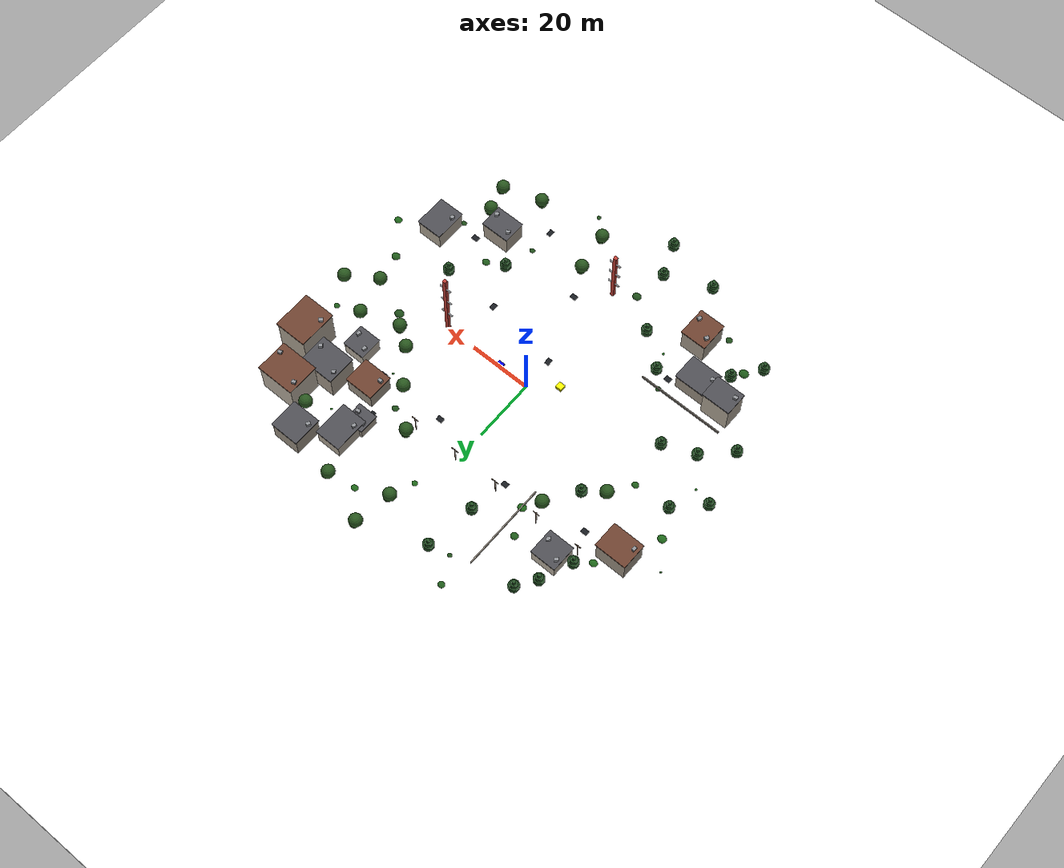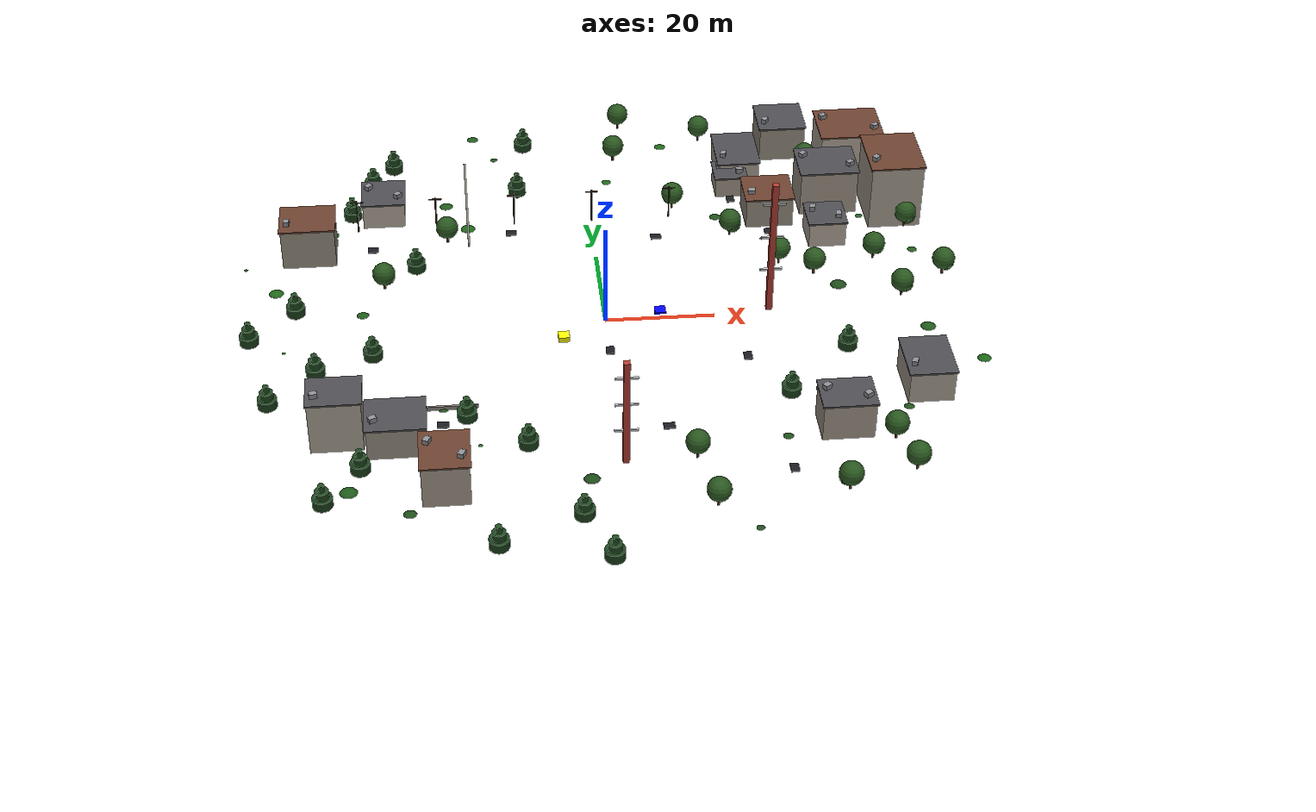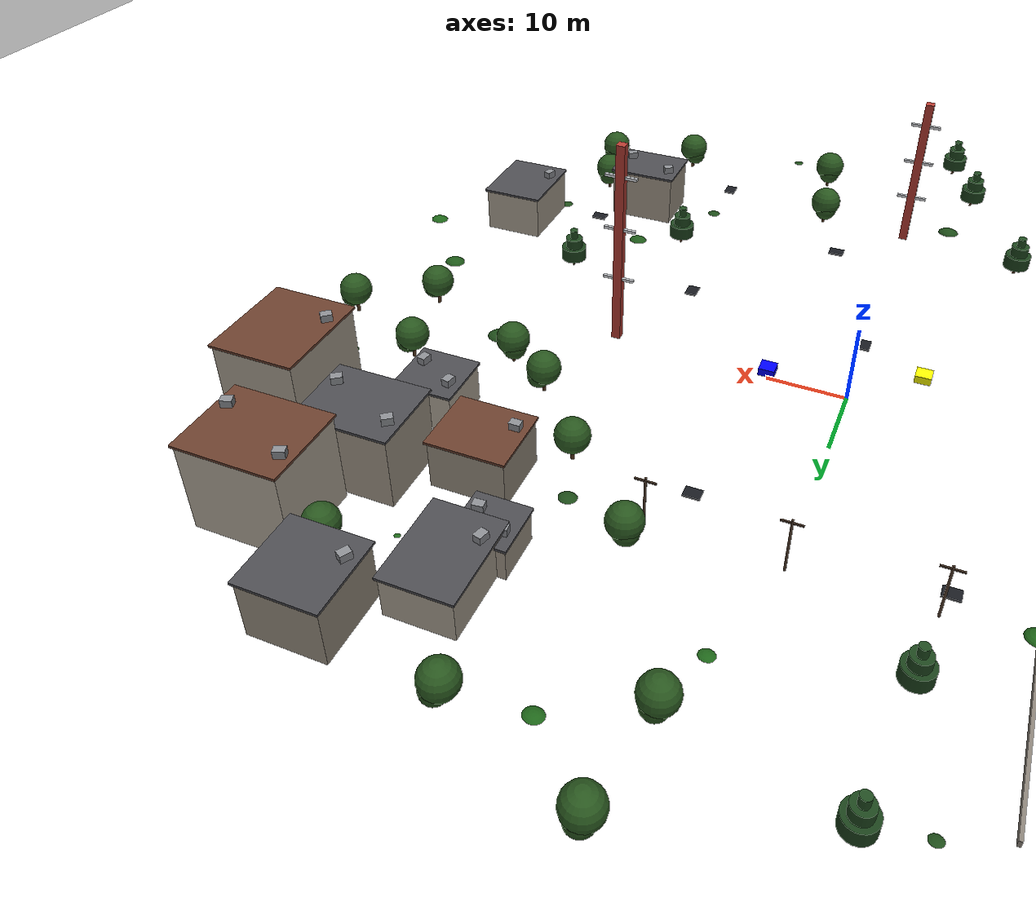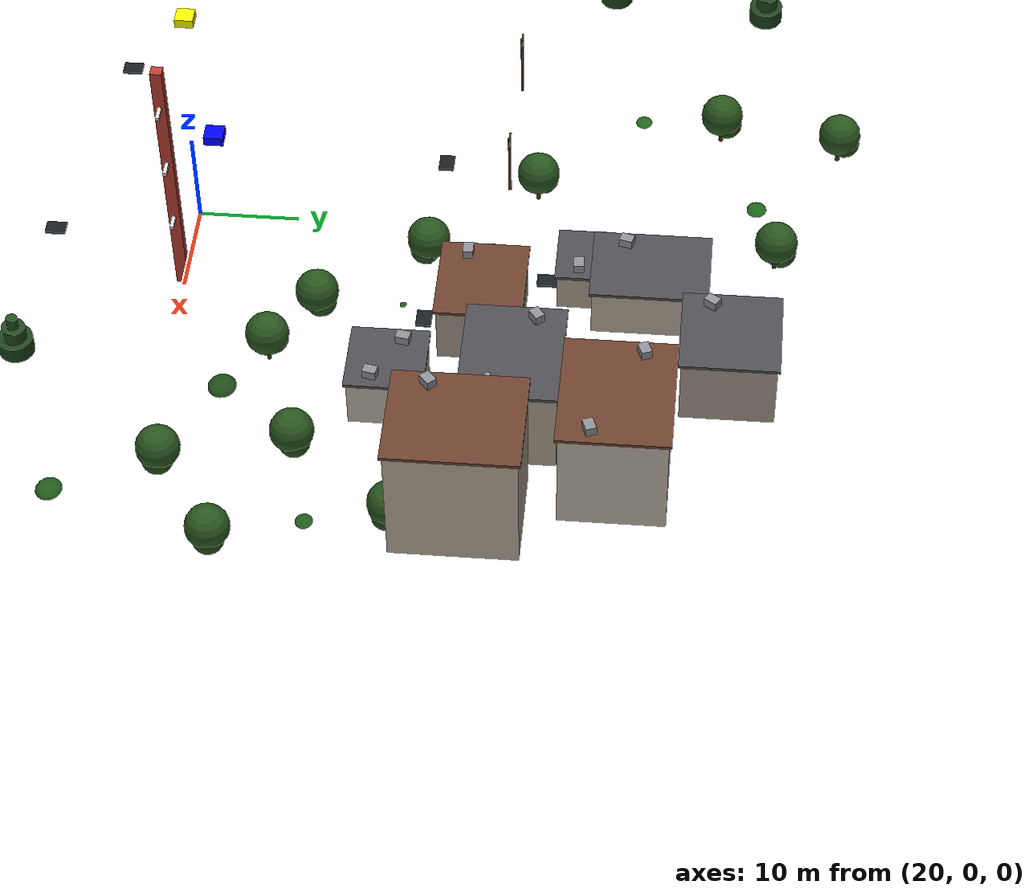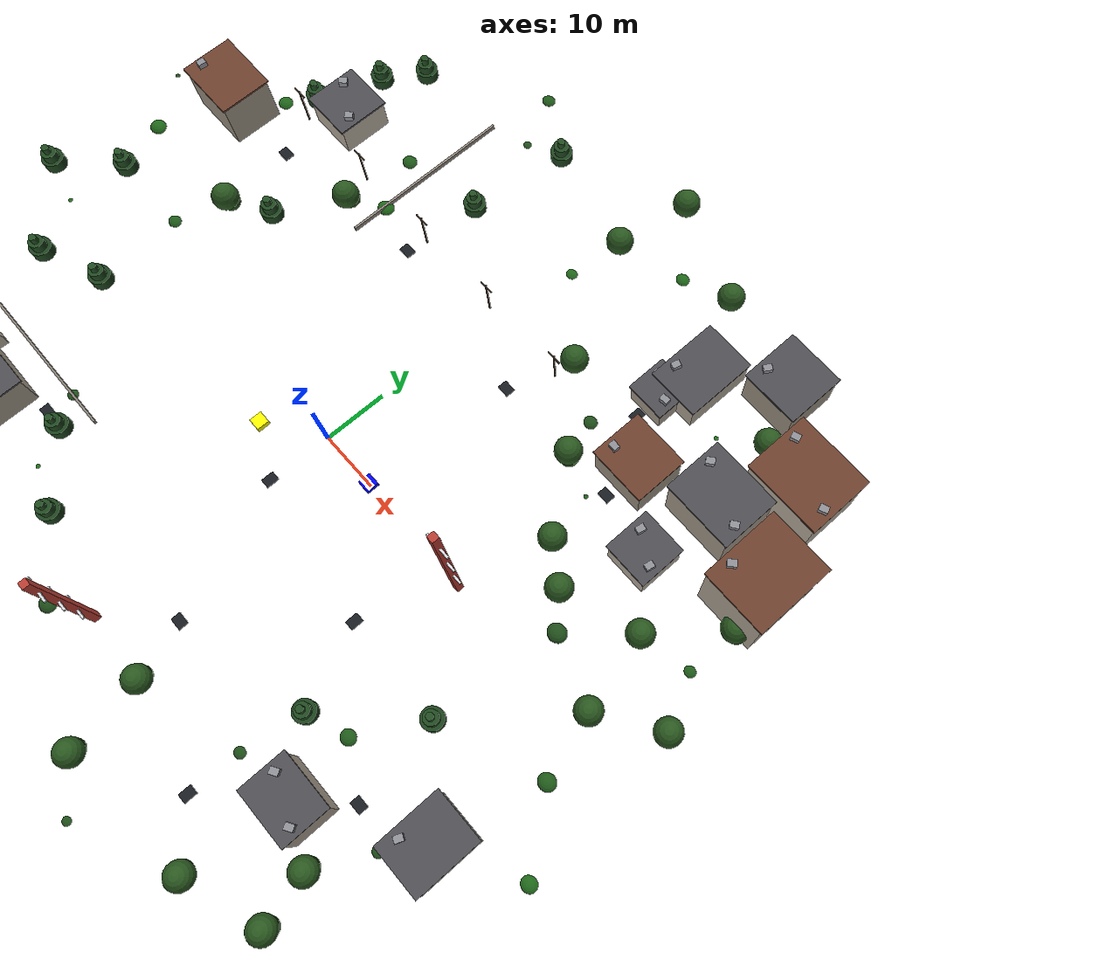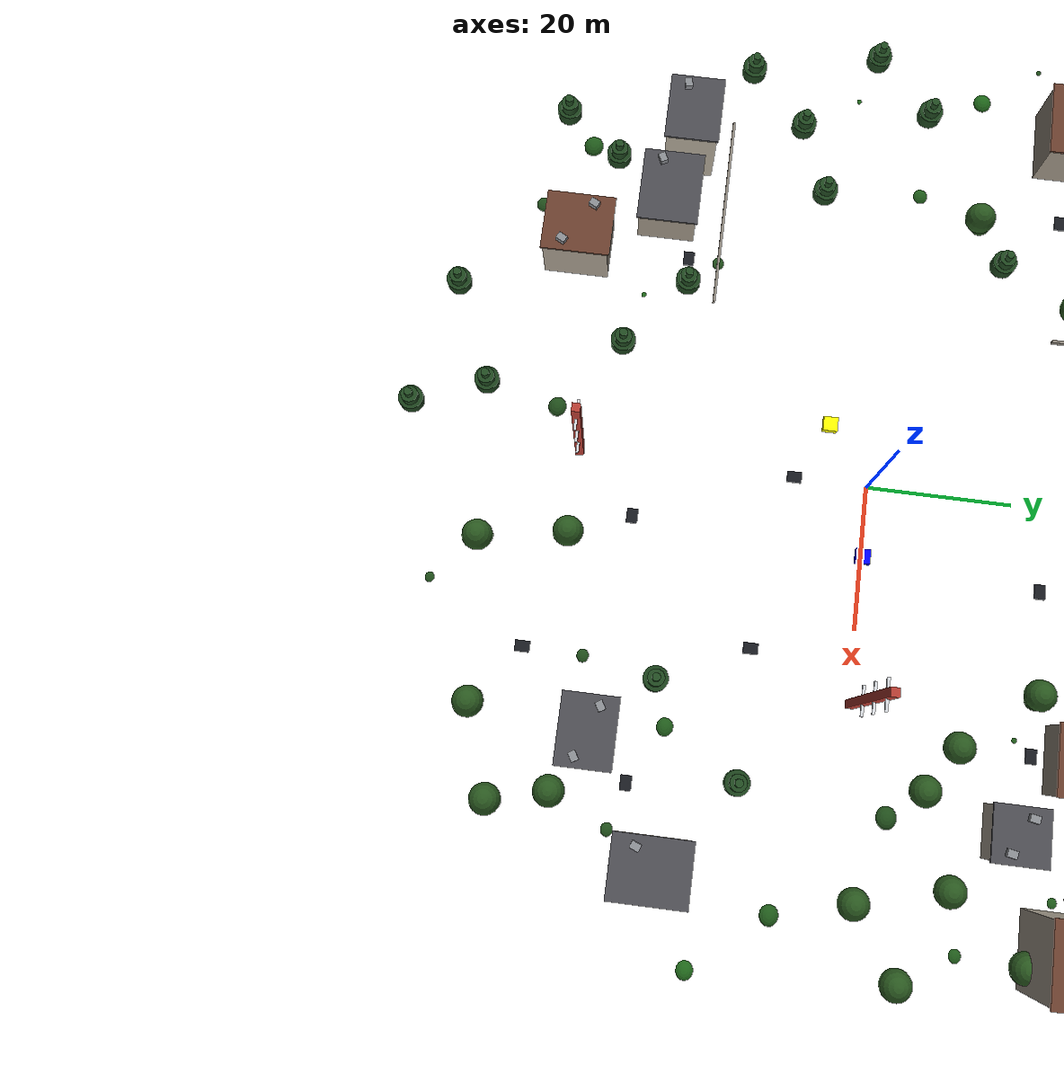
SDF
<sdf version="1.9">
 <world name="iris_runway">
  <physics name="1ms" type="ignore">
   <max_step_size>0.001</max_step_size>
   <real_time_factor>1.0</real_time_factor>
  </physics>
  <plugin filename="gz-sim-physics-system" name="gz::sim::systems::Physics"/>
  <plugin filename="gz-sim-sensors-system" name="gz::sim::systems::Sensors">
   <render_engine>ogre2</render_engine>
  </plugin>
  <plugin filename="gz-sim-user-commands-system" name="gz::sim::systems::UserCommands"/>
  <plugin filename="gz-sim-scene-broadcaster-system" name="gz::sim::systems::SceneBroadcaster"/>
  <plugin filename="gz-sim-imu-system" name="gz::sim::systems::Imu"/>
  <plugin filename="gz-sim-navsat-system" name="gz::sim::systems::NavSat"/>
  <scene>
   <ambient>0.55 0.55 0.58 1</ambient>
   <background>0.7 0.8 0.95</background>
   <shadows>true</shadows>
   <fog>
    <type>linear</type>
    <color>0.78 0.84 0.92 1</color>
    <density>0.0016</density>
    <start>60</start>
    <end>400</end>
   </fog>
  </scene>
  <spherical_coordinates>
   <latitude_deg>-35.363262</latitude_deg>
   <longitude_deg>149.165237</longitude_deg>
   <elevation>584</elevation>
   <heading_deg>0</heading_deg>
   <surface_model>EARTH_WGS84</surface_model>
  </spherical_coordinates>
  <light type="directional" name="sun">
   <pose>0 0 10 0 0 0</pose>
   <diffuse>1.0 0.98 0.92 1</diffuse>
   <specular>0.4 0.4 0.38 1</specular>
   <attenuation>
    <range>2000</range>
    <constant>0.9</constant>
    <linear>0.005</linear>
    <quadratic>0.0005</quadratic>
   </attenuation>
   <direction>-0.4 0.25 -0.88</direction>
  </light>
  <model name="ground">
   <static>true</static>
   <link name="link">
    <collision name="c">
     <geometry><plane><normal>0 0 1</normal><size>2000 2000</size></plane></geometry>
    </collision>
   </link>
  </model>
  <include><name>far_ground</name><pose>0 0 0.003 0 0 0</pose><uri>model://far_field</uri></include>
  <model name="red_pad">
   <static>true</static>
   <pose>0 10 0.03 0 0 0</pose>
   <link name="l">
    <visual name="v">
     <geometry><box><size>3 3 0.04</size></box></geometry>
     <material><ambient>1 0 0 1</ambient><diffuse>1 0 0 1</diffuse><emissive>0.4 0 0 1</emissive></material>
    </visual>
   </link>
  </model>
  <include><uri>model://aruco_marker</uri><pose>0 3 0.03 0 0 0</pose></include>
  <model name="blue_box">
   <static>true</static>
   <pose>10 0 1 0 0 0</pose>
   <link name="l">
    <visual name="v">
     <geometry><box><size>2 2 2</size></box></geometry>
     <material>
      <ambient>0 0 1 1</ambient>
      <diffuse>0 0 1 1</diffuse>
      <pbr><metal><roughness>0.6</roughness><metalness>0.0</metalness></metal></pbr>
     </material>
    </visual>
   </link>
  </model>
  <model name="yellow_box">
   <static>true</static>
   <pose>-8 -6 1 0 0 0</pose>
   <link name="l">
    <visual name="v">
     <geometry><box><size>2 2 2</size></box></geometry>
     <material>
      <ambient>1 1 0 1</ambient>
      <diffuse>1 1 0 1</diffuse>
      <pbr><metal><roughness>0.6</roughness><metalness>0.0</metalness></metal></pbr>
     </material>
    </visual>
   </link>
  </model>
  <include>
   <name>g_0_0</name>
   <pose degrees="true">-82.5 -82.5 0.01 0 0 0</pose>
   <uri>model://grass_tile_worn</uri>
  </include>
  <include>
   <name>g_0_1</name>
   <pose degrees="true">-82.5 -67.5 0.01 0 0 90</pose>
   <uri>model://grass_tile</uri>
  </include>
  <include>
   <name>g_0_2</name>
   <pose degrees="true">-82.5 -52.5 0.01 0 0 270</pose>
   <uri>model://grass_tile</uri>
  </include>
  <include>
   <name>g_0_3</name>
   <pose degrees="true">-82.5 -37.5 0.01 0 0 90</pose>
   <uri>model://grass_tile</uri>
  </include>
  <include>
   <name>g_0_4</name>
   <pose degrees="true">-82.5 -22.5 0.01 0 0 270</pose>
   <uri>model://grass_tile</uri>
  </include>
  <include>
   <name>g_0_5</name>
   <pose degrees="true">-82.5 -7.5 0.01 0 0 90</pose>
   <uri>model://grass_tile</uri>
  </include>
  <include>
   <name>g_0_6</name>
   <pose degrees="true">-82.5 7.5 0.01 0 0 270</pose>
   <uri>model://grass_tile</uri>
  </include>
  <include>
   <name>g_0_7</name>
   <pose degrees="true">-82.5 22.5 0.01 0 0 90</pose>
   <uri>model://grass_tile_worn</uri>
  </include>
  <include>
   <name>g_0_8</name>
   <pose degrees="true">-82.5 37.5 0.01 0 0 270</pose>
   <uri>model://grass_tile</uri>
  </include>
  <include>
   <name>g_0_9</name>
   <pose degrees="true">-82.5 52.5 0.01 0 0 90</pose>
   <uri>model://grass_tile</uri>
  </include>
  <include>
   <name>g_0_10</name>
   <pose degrees="true">-82.5 67.5 0.01 0 0 270</pose>
   <uri>model://grass_tile</uri>
  </include>
  <include>
   <name>g_0_11</name>
   <pose degrees="true">-82.5 82.5 0.01 0 0 90</pose>
   <uri>model://grass_tile</uri>
  </include>
  <include>
   <name>g_1_0</name>
   <pose degrees="true">-67.5 -82.5 0.01 0 0 90</pose>
   <uri>model://grass_tile</uri>
  </include>
  <include>
   <name>g_1_1</name>
   <pose degrees="true">-67.5 -67.5 0.01 0 0 0</pose>
   <uri>model://grass_tile</uri>
  </include>
  <include>
   <name>g_1_2</name>
   <pose degrees="true">-67.5 -52.5 0.01 0 0 180</pose>
   <uri>model://grass_tile</uri>
  </include>
  <include>
   <name>g_1_3</name>
   <pose degrees="true">-67.5 -37.5 0.01 0 0 0</pose>
   <uri>model://grass_tile_worn</uri>
  </include>
  <include>
   <name>g_1_4</name>
   <pose degrees="true">-67.5 -22.5 0.01 0 0 180</pose>
   <uri>model://grass_tile_worn</uri>
  </include>
  <include>
   <name>g_1_5</name>
   <pose degrees="true">-67.5 -7.5 0.01 0 0 0</pose>
   <uri>model://grass_tile_worn</uri>
  </include>
  <include>
   <name>g_1_6</name>
   <pose degrees="true">-67.5 7.5 0.01 0 0 180</pose>
   <uri>model://grass_tile</uri>
  </include>
  <include>
   <name>g_1_7</name>
   <pose degrees="true">-67.5 22.5 0.01 0 0 0</pose>
   <uri>model://grass_tile</uri>
  </include>
  <include>
   <name>g_1_8</name>
   <pose degrees="true">-67.5 37.5 0.01 0 0 180</pose>
   <uri>model://grass_tile</uri>
  </include>
  <include>
   <name>g_1_9</name>
   <pose degrees="true">-67.5 52.5 0.01 0 0 0</pose>
   <uri>model://grass_tile_worn</uri>
  </include>
  <include>
   <name>g_1_10</name>
   <pose degrees="true">-67.5 67.5 0.01 0 0 180</pose>
   <uri>model://grass_tile</uri>
  </include>
  <include>
   <name>g_1_11</name>
   <pose degrees="true">-67.5 82.5 0.01 0 0 0</pose>
   <uri>model://grass_tile</uri>
  </include>
  <include>
   <name>g_2_0</name>
   <pose degrees="true">-52.5 -82.5 0.01 0 0 270</pose>
   <uri>model://grass_tile</uri>
  </include>
  <include>
   <name>g_2_1</name>
   <pose degrees="true">-52.5 -67.5 0.01 0 0 180</pose>
   <uri>model://grass_tile</uri>
  </include>
  <include>
   <name>g_2_2</name>
   <pose degrees="true">-52.5 -52.5 0.01 0 0 0</pose>
   <uri>model://grass_tile</uri>
  </include>
  <include>
   <name>g_2_3</name>
   <pose degrees="true">-52.5 -37.5 0.01 0 0 180</pose>
   <uri>model://grass_tile</uri>
  </include>
  <include>
   <name>g_2_4</name>
   <pose degrees="true">-52.5 -22.5 0.01 0 0 0</pose>
   <uri>model://grass_tile</uri>
  </include>
  <include>
   <name>g_2_5</name>
   <pose degrees="true">-52.5 -7.5 0.01 0 0 180</pose>
   <uri>model://grass_tile</uri>
  </include>
  <include>
   <name>g_2_6</name>
   <pose degrees="true">-52.5 7.5 0.01 0 0 0</pose>
   <uri>model://grass_tile_worn</uri>
  </include>
  <include>
   <name>g_2_7</name>
   <pose degrees="true">-52.5 22.5 0.01 0 0 180</pose>
   <uri>model://grass_tile</uri>
  </include>
  <include>
   <name>g_2_8</name>
   <pose degrees="true">-52.5 37.5 0.01 0 0 0</pose>
   <uri>model://grass_tile_worn</uri>
  </include>
  <include>
   <name>g_2_9</name>
   <pose degrees="true">-52.5 52.5 0.01 0 0 180</pose>
   <uri>model://grass_tile</uri>
  </include>
  <include>
   <name>g_2_10</name>
   <pose degrees="true">-52.5 67.5 0.01 0 0 0</pose>
   <uri>model://grass_tile_worn</uri>
  </include>
  <include>
   <name>g_2_11</name>
   <pose degrees="true">-52.5 82.5 0.01 0 0 180</pose>
   <uri>model://grass_tile</uri>
  </include>
  <include>
   <name>g_3_0</name>
   <pose degrees="true">-37.5 -82.5 0.01 0 0 90</pose>
   <uri>model://grass_tile</uri>
  </include>
  <include>
   <name>g_3_1</name>
   <pose degrees="true">-37.5 -67.5 0.01 0 0 0</pose>
   <uri>model://grass_tile</uri>
  </include>
  <include>
   <name>g_3_2</name>
   <pose degrees="true">-37.5 -52.5 0.01 0 0 180</pose>
   <uri>model://grass_tile</uri>
  </include>
  <include>
   <name>g_3_3</name>
   <pose degrees="true">-37.5 -37.5 0.01 0 0 0</pose>
   <uri>model://grass_tile</uri>
  </include>
  <include>
   <name>g_3_4</name>
   <pose degrees="true">-37.5 -22.5 0.01 0 0 180</pose>
   <uri>model://grass_tile</uri>
  </include>
  <include>
   <name>g_3_5</name>
   <pose degrees="true">-37.5 -7.5 0.01 0 0 0</pose>
   <uri>model://grass_tile</uri>
  </include>
  <include>
   <name>g_3_6</name>
   <pose degrees="true">-37.5 7.5 0.01 0 0 180</pose>
   <uri>model://grass_tile</uri>
  </include>
  <include>
   <name>g_3_7</name>
   <pose degrees="true">-37.5 22.5 0.01 0 0 0</pose>
   <uri>model://grass_tile_worn</uri>
  </include>
  <include>
   <name>g_3_8</name>
   <pose degrees="true">-37.5 37.5 0.01 0 0 180</pose>
   <uri>model://grass_tile</uri>
  </include>
  <include>
   <name>g_3_9</name>
   <pose degrees="true">-37.5 52.5 0.01 0 0 0</pose>
   <uri>model://grass_tile</uri>
  </include>
  <include>
   <name>g_3_10</name>
   <pose degrees="true">-37.5 67.5 0.01 0 0 180</pose>
   <uri>model://grass_tile</uri>
  </include>
  <include>
   <name>g_3_11</name>
   <pose degrees="true">-37.5 82.5 0.01 0 0 0</pose>
   <uri>model://grass_tile</uri>
  </include>
  <include>
   <name>g_4_0</name>
   <pose degrees="true">-22.5 -82.5 0.01 0 0 270</pose>
   <uri>model://grass_tile</uri>
  </include>
  <include>
   <name>g_4_1</name>
   <pose degrees="true">-22.5 -67.5 0.01 0 0 180</pose>
   <uri>model://grass_tile</uri>
  </include>
  <include>
   <name>g_4_2</name>
   <pose degrees="true">-22.5 -52.5 0.01 0 0 0</pose>
   <uri>model://grass_tile</uri>
  </include>
  <include>
   <name>g_4_3</name>
   <pose degrees="true">-22.5 -37.5 0.01 0 0 180</pose>
   <uri>model://grass_tile</uri>
  </include>
  <include>
   <name>g_4_4</name>
   <pose degrees="true">-22.5 -22.5 0.01 0 0 0</pose>
   <uri>model://grass_tile</uri>
  </include>
  <include>
   <name>g_4_5</name>
   <pose degrees="true">-22.5 -7.5 0.01 0 0 180</pose>
   <uri>model://grass_tile</uri>
  </include>
  <include>
   <name>g_4_6</name>
   <pose degrees="true">-22.5 7.5 0.01 0 0 0</pose>
   <uri>model://grass_tile</uri>
  </include>
  <include>
   <name>g_4_7</name>
   <pose degrees="true">-22.5 22.5 0.01 0 0 180</pose>
   <uri>model://grass_tile</uri>
  </include>
  <include>
   <name>g_4_8</name>
   <pose degrees="true">-22.5 37.5 0.01 0 0 0</pose>
   <uri>model://grass_tile</uri>
  </include>
  <include>
   <name>g_4_9</name>
   <pose degrees="true">-22.5 52.5 0.01 0 0 180</pose>
   <uri>model://grass_tile</uri>
  </include>
  <include>
   <name>g_4_10</name>
   <pose degrees="true">-22.5 67.5 0.01 0 0 0</pose>
   <uri>model://grass_tile</uri>
  </include>
  <include>
   <name>g_4_11</name>
   <pose degrees="true">-22.5 82.5 0.01 0 0 180</pose>
   <uri>model://grass_tile</uri>
  </include>
  <include>
   <name>g_5_0</name>
   <pose degrees="true">-7.5 -82.5 0.01 0 0 90</pose>
   <uri>model://grass_tile</uri>
  </include>
  <include>
   <name>g_5_1</name>
   <pose degrees="true">-7.5 -67.5 0.01 0 0 0</pose>
   <uri>model://grass_tile_worn</uri>
  </include>
  <include>
   <name>g_5_2</name>
   <pose degrees="true">-7.5 -52.5 0.01 0 0 180</pose>
   <uri>model://grass_tile</uri>
  </include>
  <include>
   <name>g_5_3</name>
   <pose degrees="true">-7.5 -37.5 0.01 0 0 0</pose>
   <uri>model://grass_tile_worn</uri>
  </include>
  <include>
   <name>g_5_4</name>
   <pose degrees="true">-7.5 -22.5 0.01 0 0 180</pose>
   <uri>model://grass_tile</uri>
  </include>
  <include>
   <name>g_5_5</name>
   <pose degrees="true">-7.5 -7.5 0.01 0 0 0</pose>
   <uri>model://grass_tile</uri>
  </include>
  <include>
   <name>g_5_6</name>
   <pose degrees="true">-7.5 7.5 0.01 0 0 180</pose>
   <uri>model://grass_tile</uri>
  </include>
  <include>
   <name>g_5_7</name>
   <pose degrees="true">-7.5 22.5 0.01 0 0 0</pose>
   <uri>model://grass_tile</uri>
  </include>
  <include>
   <name>g_5_8</name>
   <pose degrees="true">-7.5 37.5 0.01 0 0 180</pose>
   <uri>model://grass_tile</uri>
  </include>
  <include>
   <name>g_5_9</name>
   <pose degrees="true">-7.5 52.5 0.01 0 0 0</pose>
   <uri>model://grass_tile</uri>
  </include>
  <include>
   <name>g_5_10</name>
   <pose degrees="true">-7.5 67.5 0.01 0 0 180</pose>
   <uri>model://grass_tile</uri>
  </include>
  <include>
   <name>g_5_11</name>
   <pose degrees="true">-7.5 82.5 0.01 0 0 0</pose>
   <uri>model://grass_tile</uri>
  </include>
  <include>
   <name>g_6_0</name>
   <pose degrees="true">7.5 -82.5 0.01 0 0 180</pose>
   <uri>model://grass_tile</uri>
  </include>
  <include>
   <name>g_6_1</name>
   <pose degrees="true">7.5 -67.5 0.01 0 0 270</pose>
   <uri>model://grass_tile</uri>
  </include>
  <include>
   <name>g_6_2</name>
   <pose degrees="true">7.5 -52.5 0.01 0 0 90</pose>
   <uri>model://grass_tile</uri>
  </include>
  <include>
   <name>g_6_3</name>
   <pose degrees="true">7.5 -37.5 0.01 0 0 270</pose>
   <uri>model://grass_tile</uri>
  </include>
  <include>
   <name>g_6_4</name>
   <pose degrees="true">7.5 -22.5 0.01 0 0 90</pose>
   <uri>model://grass_tile</uri>
  </include>
  <include>
   <name>g_6_5</name>
   <pose degrees="true">7.5 -7.5 0.01 0 0 270</pose>
   <uri>model://grass_tile</uri>
  </include>
  <include>
   <name>g_6_6</name>
   <pose degrees="true">7.5 7.5 0.01 0 0 90</pose>
   <uri>model://grass_tile</uri>
  </include>
  <include>
   <name>g_6_7</name>
   <pose degrees="true">7.5 22.5 0.01 0 0 270</pose>
   <uri>model://grass_tile</uri>
  </include>
  <include>
   <name>g_6_8</name>
   <pose degrees="true">7.5 37.5 0.01 0 0 90</pose>
   <uri>model://grass_tile</uri>
  </include>
  <include>
   <name>g_6_9</name>
   <pose degrees="true">7.5 52.5 0.01 0 0 270</pose>
   <uri>model://grass_tile</uri>
  </include>
  <include>
   <name>g_6_10</name>
   <pose degrees="true">7.5 67.5 0.01 0 0 90</pose>
   <uri>model://grass_tile</uri>
  </include>
  <include>
   <name>g_6_11</name>
   <pose degrees="true">7.5 82.5 0.01 0 0 270</pose>
   <uri>model://grass_tile</uri>
  </include>
  <include>
   <name>g_7_0</name>
   <pose degrees="true">22.5 -82.5 0.01 0 0 0</pose>
   <uri>model://grass_tile_worn</uri>
  </include>
  <include>
   <name>g_7_1</name>
   <pose degrees="true">22.5 -67.5 0.01 0 0 90</pose>
   <uri>model://grass_tile</uri>
  </include>
  <include>
   <name>g_7_2</name>
   <pose degrees="true">22.5 -52.5 0.01 0 0 270</pose>
   <uri>model://grass_tile</uri>
  </include>
  <include>
   <name>g_7_3</name>
   <pose degrees="true">22.5 -37.5 0.01 0 0 90</pose>
   <uri>model://grass_tile_worn</uri>
  </include>
  <include>
   <name>g_7_4</name>
   <pose degrees="true">22.5 -22.5 0.01 0 0 270</pose>
   <uri>model://grass_tile</uri>
  </include>
  <include>
   <name>g_7_5</name>
   <pose degrees="true">22.5 -7.5 0.01 0 0 90</pose>
   <uri>model://grass_tile</uri>
  </include>
  <include>
   <name>g_7_6</name>
   <pose degrees="true">22.5 7.5 0.01 0 0 270</pose>
   <uri>model://grass_tile_worn</uri>
  </include>
  <include>
   <name>g_7_7</name>
   <pose degrees="true">22.5 22.5 0.01 0 0 90</pose>
   <uri>model://grass_tile</uri>
  </include>
  <include>
   <name>g_7_8</name>
   <pose degrees="true">22.5 37.5 0.01 0 0 270</pose>
   <uri>model://grass_tile</uri>
  </include>
  <include>
   <name>g_7_9</name>
   <pose degrees="true">22.5 52.5 0.01 0 0 90</pose>
   <uri>model://grass_tile</uri>
  </include>
  <include>
   <name>g_7_10</name>
   <pose degrees="true">22.5 67.5 0.01 0 0 270</pose>
   <uri>model://grass_tile_worn</uri>
  </include>
  <include>
   <name>g_7_11</name>
   <pose degrees="true">22.5 82.5 0.01 0 0 90</pose>
   <uri>model://grass_tile</uri>
  </include>
  <include>
   <name>g_8_0</name>
   <pose degrees="true">37.5 -82.5 0.01 0 0 180</pose>
   <uri>model://grass_tile</uri>
  </include>
  <include>
   <name>g_8_1</name>
   <pose degrees="true">37.5 -67.5 0.01 0 0 270</pose>
   <uri>model://grass_tile</uri>
  </include>
  <include>
   <name>g_8_2</name>
   <pose degrees="true">37.5 -52.5 0.01 0 0 90</pose>
   <uri>model://grass_tile</uri>
  </include>
  <include>
   <name>g_8_3</name>
   <pose degrees="true">37.5 -37.5 0.01 0 0 270</pose>
   <uri>model://grass_tile</uri>
  </include>
  <include>
   <name>g_8_4</name>
   <pose degrees="true">37.5 -22.5 0.01 0 0 90</pose>
   <uri>model://grass_tile</uri>
  </include>
  <include>
   <name>g_8_5</name>
   <pose degrees="true">37.5 -7.5 0.01 0 0 270</pose>
   <uri>model://grass_tile</uri>
  </include>
  <include>
   <name>g_8_6</name>
   <pose degrees="true">37.5 7.5 0.01 0 0 90</pose>
   <uri>model://grass_tile</uri>
  </include>
  <include>
   <name>g_8_7</name>
   <pose degrees="true">37.5 22.5 0.01 0 0 270</pose>
   <uri>model://grass_tile</uri>
  </include>
  <include>
   <name>g_8_8</name>
   <pose degrees="true">37.5 37.5 0.01 0 0 90</pose>
   <uri>model://grass_tile</uri>
  </include>
  <include>
   <name>g_8_9</name>
   <pose degrees="true">37.5 52.5 0.01 0 0 270</pose>
   <uri>model://grass_tile</uri>
  </include>
  <include>
   <name>g_8_10</name>
   <pose degrees="true">37.5 67.5 0.01 0 0 90</pose>
   <uri>model://grass_tile</uri>
  </include>
  <include>
   <name>g_8_11</name>
   <pose degrees="true">37.5 82.5 0.01 0 0 270</pose>
   <uri>model://grass_tile_worn</uri>
  </include>
  <include>
   <name>g_9_0</name>
   <pose degrees="true">52.5 -82.5 0.01 0 0 0</pose>
   <uri>model://grass_tile</uri>
  </include>
  <include>
   <name>g_9_1</name>
   <pose degrees="true">52.5 -67.5 0.01 0 0 90</pose>
   <uri>model://grass_tile</uri>
  </include>
  <include>
   <name>g_9_2</name>
   <pose degrees="true">52.5 -52.5 0.01 0 0 270</pose>
   <uri>model://grass_tile</uri>
  </include>
  <include>
   <name>g_9_3</name>
   <pose degrees="true">52.5 -37.5 0.01 0 0 90</pose>
   <uri>model://grass_tile</uri>
  </include>
  <include>
   <name>g_9_4</name>
   <pose degrees="true">52.5 -22.5 0.01 0 0 270</pose>
   <uri>model://grass_tile</uri>
  </include>
  <include>
   <name>g_9_5</name>
   <pose degrees="true">52.5 -7.5 0.01 0 0 90</pose>
   <uri>model://grass_tile</uri>
  </include>
  <include>
   <name>g_9_6</name>
   <pose degrees="true">52.5 7.5 0.01 0 0 270</pose>
   <uri>model://grass_tile_worn</uri>
  </include>
  <include>
   <name>g_9_7</name>
   <pose degrees="true">52.5 22.5 0.01 0 0 90</pose>
   <uri>model://grass_tile</uri>
  </include>
  <include>
   <name>g_9_8</name>
   <pose degrees="true">52.5 37.5 0.01 0 0 270</pose>
   <uri>model://grass_tile</uri>
  </include>
  <include>
   <name>g_9_9</name>
   <pose degrees="true">52.5 52.5 0.01 0 0 90</pose>
   <uri>model://grass_tile</uri>
  </include>
  <include>
   <name>g_9_10</name>
   <pose degrees="true">52.5 67.5 0.01 0 0 270</pose>
   <uri>model://grass_tile</uri>
  </include>
  <include>
   <name>g_9_11</name>
   <pose degrees="true">52.5 82.5 0.01 0 0 90</pose>
   <uri>model://grass_tile_worn</uri>
  </include>
  <include>
   <name>g_10_0</name>
   <pose degrees="true">67.5 -82.5 0.01 0 0 180</pose>
   <uri>model://grass_tile</uri>
  </include>
  <include>
   <name>g_10_1</name>
   <pose degrees="true">67.5 -67.5 0.01 0 0 270</pose>
   <uri>model://grass_tile</uri>
  </include>
  <include>
   <name>g_10_2</name>
   <pose degrees="true">67.5 -52.5 0.01 0 0 90</pose>
   <uri>model://grass_tile_worn</uri>
  </include>
  <include>
   <name>g_10_3</name>
   <pose degrees="true">67.5 -37.5 0.01 0 0 270</pose>
   <uri>model://grass_tile</uri>
  </include>
  <include>
   <name>g_10_4</name>
   <pose degrees="true">67.5 -22.5 0.01 0 0 90</pose>
   <uri>model://grass_tile</uri>
  </include>
  <include>
   <name>g_10_5</name>
   <pose degrees="true">67.5 -7.5 0.01 0 0 270</pose>
   <uri>model://grass_tile</uri>
  </include>
  <include>
   <name>g_10_6</name>
   <pose degrees="true">67.5 7.5 0.01 0 0 90</pose>
   <uri>model://grass_tile_worn</uri>
  </include>
  <include>
   <name>g_10_7</name>
   <pose degrees="true">67.5 22.5 0.01 0 0 270</pose>
   <uri>model://grass_tile</uri>
  </include>
  <include>
   <name>g_10_8</name>
   <pose degrees="true">67.5 37.5 0.01 0 0 90</pose>
   <uri>model://grass_tile</uri>
  </include>
  <include>
   <name>g_10_9</name>
   <pose degrees="true">67.5 52.5 0.01 0 0 270</pose>
   <uri>model://grass_tile</uri>
  </include>
  <include>
   <name>g_10_10</name>
   <pose degrees="true">67.5 67.5 0.01 0 0 90</pose>
   <uri>model://grass_tile</uri>
  </include>
  <include>
   <name>g_10_11</name>
   <pose degrees="true">67.5 82.5 0.01 0 0 270</pose>
   <uri>model://grass_tile</uri>
  </include>
  <include>
   <name>g_11_0</name>
   <pose degrees="true">82.5 -82.5 0.01 0 0 270</pose>
   <uri>model://grass_tile</uri>
  </include>
  <include>
   <name>g_11_1</name>
   <pose degrees="true">82.5 -67.5 0.01 0 0 180</pose>
   <uri>model://grass_tile</uri>
  </include>
  <include>
   <name>g_11_2</name>
   <pose degrees="true">82.5 -52.5 0.01 0 0 0</pose>
   <uri>model://grass_tile</uri>
  </include>
  <include>
   <name>g_11_3</name>
   <pose degrees="true">82.5 -37.5 0.01 0 0 180</pose>
   <uri>model://grass_tile</uri>
  </include>
  <include>
   <name>g_11_4</name>
   <pose degrees="true">82.5 -22.5 0.01 0 0 0</pose>
   <uri>model://grass_tile</uri>
  </include>
  <include>
   <name>g_11_5</name>
   <pose degrees="true">82.5 -7.5 0.01 0 0 180</pose>
   <uri>model://grass_tile</uri>
  </include>
  <include>
   <name>g_11_6</name>
   <pose degrees="true">82.5 7.5 0.01 0 0 0</pose>
   <uri>model://grass_tile</uri>
  </include>
  <include>
   <name>g_11_7</name>
   <pose degrees="true">82.5 22.5 0.01 0 0 180</pose>
   <uri>model://grass_tile</uri>
  </include>
  <include>
   <name>g_11_8</name>
   <pose degrees="true">82.5 37.5 0.01 0 0 0</pose>
   <uri>model://grass_tile_worn</uri>
  </include>
  <include>
   <name>g_11_9</name>
   <pose degrees="true">82.5 52.5 0.01 0 0 180</pose>
   <uri>model://grass_tile_worn</uri>
  </include>
  <include>
   <name>g_11_10</name>
   <pose degrees="true">82.5 67.5 0.01 0 0 0</pose>
   <uri>model://grass_tile</uri>
  </include>
  <include>
   <name>g_11_11</name>
   <pose degrees="true">82.5 82.5 0.01 0 0 180</pose>
   <uri>model://grass_tile_worn</uri>
  </include>
  <include><name>tree_0</name><pose>26 24 0 0 0 0.0</pose><uri>model://tree_oak</uri></include>
  <include><name>tree_1</name><pose>30 -26 0 0 0 0.7</pose><uri>model://tree_pine</uri></include>
  <include><name>tree_2</name><pose>-28 26 0 0 0 1.4</pose><uri>model://tree_oak</uri></include>
  <include><name>tree_3</name><pose>-26 -28 0 0 0 2.1</pose><uri>model://tree_pine</uri></include>
  <include><name>tree_4</name><pose>40 10 0 0 0 2.8</pose><uri>model://tree_oak</uri></include>
  <include><name>tree_5</name><pose>42 -14 0 0 0 0.4</pose><uri>model://tree_pine</uri></include>
  <include><name>tree_6</name><pose>-40 12 0 0 0 1.1</pose><uri>model://tree_oak</uri></include>
  <include><name>tree_7</name><pose>-42 -10 0 0 0 1.8</pose><uri>model://tree_pine</uri></include>
  <include><name>tree_8</name><pose>12 -40 0 0 0 2.5</pose><uri>model://tree_oak</uri></include>
  <include><name>tree_9</name><pose>-14 40 0 0 0 0.1</pose><uri>model://tree_pine</uri></include>
  <include><name>tree_10</name><pose>48 36 0 0 0 0.8</pose><uri>model://tree_oak</uri></include>
  <include><name>tree_11</name><pose>-46 34 0 0 0 1.5</pose><uri>model://tree_pine</uri></include>
  <include><name>tree_12</name><pose>46 -38 0 0 0 2.2</pose><uri>model://tree_oak</uri></include>
  <include><name>tree_13</name><pose>-44 -40 0 0 0 2.9</pose><uri>model://tree_pine</uri></include>
  <include><name>tree_14</name><pose>55 2 0 0 0 0.5</pose><uri>model://tree_oak</uri></include>
  <include><name>tree_15</name><pose>-56 4 0 0 0 1.2</pose><uri>model://tree_pine</uri></include>
  <include><name>tree_16</name><pose>6 52 0 0 0 1.9</pose><uri>model://tree_oak</uri></include>
  <include><name>tree_17</name><pose>-8 -54 0 0 0 2.6</pose><uri>model://tree_pine</uri></include>
  <include><name>tree_18</name><pose>60 24 0 0 0 0.2</pose><uri>model://tree_oak</uri></include>
  <include><name>tree_19</name><pose>-60 -22 0 0 0 0.9</pose><uri>model://tree_pine</uri></include>
  <include><name>tree_20</name><pose>24 58 0 0 0 1.6</pose><uri>model://tree_oak</uri></include>
  <include><name>tree_21</name><pose>-22 -60 0 0 0 2.3</pose><uri>model://tree_pine</uri></include>
  <include><name>tree_22</name><pose>36 -50 0 0 0 3.0</pose><uri>model://tree_oak</uri></include>
  <include><name>tree_23</name><pose>-38 50 0 0 0 0.6</pose><uri>model://tree_pine</uri></include>
  <include><name>tree_24</name><pose>34 14 0 0 0 1.3</pose><uri>model://tree_oak</uri></include>
  <include><name>tree_25</name><pose>-34 16 0 0 0 2.0</pose><uri>model://tree_pine</uri></include>
  <include><name>tree_26</name><pose>16 34 0 0 0 2.7</pose><uri>model://tree_oak</uri></include>
  <include><name>tree_27</name><pose>-16 -36 0 0 0 0.3</pose><uri>model://tree_pine</uri></include>
  <include><name>tree_28</name><pose>52 14 0 0 0 1.0</pose><uri>model://tree_oak</uri></include>
  <include><name>tree_29</name><pose>-52 -14 0 0 0 1.7</pose><uri>model://tree_pine</uri></include>
  <include><name>tree_30</name><pose>14 -52 0 0 0 2.4</pose><uri>model://tree_oak</uri></include>
  <include><name>tree_31</name><pose>-12 56 0 0 0 3.1</pose><uri>model://tree_pine</uri></include>
  <include><name>tree_32</name><pose>64 8 0 0 0 0.7</pose><uri>model://tree_oak</uri></include>
  <include><name>tree_33</name><pose>-64 -4 0 0 0 1.4</pose><uri>model://tree_pine</uri></include>
  <include><name>tree_34</name><pose>8 64 0 0 0 2.1</pose><uri>model://tree_oak</uri></include>
  <include><name>tree_35</name><pose>-4 -64 0 0 0 2.8</pose><uri>model://tree_pine</uri></include>
  <include><name>tree_36</name><pose>44 46 0 0 0 0.4</pose><uri>model://tree_oak</uri></include>
  <include><name>tree_37</name><pose>-42 44 0 0 0 1.1</pose><uri>model://tree_pine</uri></include>
  <include><name>tree_38</name><pose>48 -46 0 0 0 1.8</pose><uri>model://tree_oak</uri></include>
  <include><name>tree_39</name><pose>-50 -48 0 0 0 2.5</pose><uri>model://tree_pine</uri></include>
  <model name="bldg_0">
   <static>true</static>
   <pose>34 30 0 0 0 0</pose>
   <link name="l">
    <visual name="walls">
     <pose degrees="true">0 0 3.5 0 0 0</pose>
     <geometry><box><size>9 8 7</size></box></geometry>
     <material>
      <ambient>0.34 0.32 0.29 1</ambient>
      <diffuse>0.62 0.58 0.52 1</diffuse>
      <pbr><metal><roughness>0.85</roughness><metalness>0.0</metalness></metal></pbr>
     </material>
    </visual>
    <visual name="roof">
     <pose degrees="true">0 0 7.15 0 0 0</pose>
     <geometry><box><size>9.5 8.5 0.3</size></box></geometry>
     <material>
      <ambient>0.23 0.14 0.10 1</ambient>
      <diffuse>0.42 0.25 0.18 1</diffuse>
      <pbr><metal><roughness>0.9</roughness><metalness>0.0</metalness></metal></pbr>
     </material>
    </visual>
    <collision name="c">
     <pose>0 0 3.65 0 0 0</pose>
     <geometry><box><size>9 8 7.3</size></box></geometry>
    </collision>
    <visual name="ac_0">
     <pose degrees="true">-3.3 -1.6 7.75 0 0 0</pose>
     <geometry><box><size>1.3 1.0 0.9</size></box></geometry>
     <material>
      <ambient>0.30 0.31 0.32 1</ambient>
      <diffuse>0.55 0.56 0.58 1</diffuse>
      <pbr><metal><roughness>0.5</roughness><metalness>0.6</metalness></metal></pbr>
     </material>
    </visual>
   </link>
  </model>
  <model name="bldg_1">
   <static>true</static>
   <pose>46 34 0 0 0 0</pose>
   <link name="l">
    <visual name="walls">
     <pose degrees="true">0 0 5.0 0 0 0</pose>
     <geometry><box><size>11 9 10</size></box></geometry>
     <material>
      <ambient>0.36 0.34 0.31 1</ambient>
      <diffuse>0.66 0.62 0.56 1</diffuse>
      <pbr><metal><roughness>0.85</roughness><metalness>0.0</metalness></metal></pbr>
     </material>
    </visual>
    <visual name="roof">
     <pose degrees="true">0 0 10.15 0 0 0</pose>
     <geometry><box><size>11.5 9.5 0.3</size></box></geometry>
     <material>
      <ambient>0.17 0.17 0.18 1</ambient>
      <diffuse>0.30 0.30 0.32 1</diffuse>
      <pbr><metal><roughness>0.9</roughness><metalness>0.0</metalness></metal></pbr>
     </material>
    </visual>
    <collision name="c">
     <pose>0 0 5.15 0 0 0</pose>
     <geometry><box><size>11 9 10.3</size></box></geometry>
    </collision>
    <visual name="ac_0">
     <pose degrees="true">4.3 -1.9 10.75 0 0 37</pose>
     <geometry><box><size>1.3 1.0 0.9</size></box></geometry>
     <material>
      <ambient>0.30 0.31 0.32 1</ambient>
      <diffuse>0.55 0.56 0.58 1</diffuse>
      <pbr><metal><roughness>0.5</roughness><metalness>0.6</metalness></metal></pbr>
     </material>
    </visual>
    <visual name="ac_1">
     <pose degrees="true">-4.3 1.9 10.75 0 0 37</pose>
     <geometry><box><size>1.3 1.0 0.9</size></box></geometry>
     <material>
      <ambient>0.30 0.31 0.32 1</ambient>
      <diffuse>0.55 0.56 0.58 1</diffuse>
      <pbr><metal><roughness>0.5</roughness><metalness>0.6</metalness></metal></pbr>
     </material>
    </visual>
   </link>
  </model>
  <model name="bldg_2">
   <static>true</static>
   <pose>30 46 0 0 0 0</pose>
   <link name="l">
    <visual name="walls">
     <pose degrees="true">0 0 3.0 0 0 0</pose>
     <geometry><box><size>8 11 6</size></box></geometry>
     <material>
      <ambient>0.39 0.36 0.33 1</ambient>
      <diffuse>0.70 0.66 0.60 1</diffuse>
      <pbr><metal><roughness>0.85</roughness><metalness>0.0</metalness></metal></pbr>
     </material>
    </visual>
    <visual name="roof">
     <pose degrees="true">0 0 6.15 0 0 0</pose>
     <geometry><box><size>8.5 11.5 0.3</size></box></geometry>
     <material>
      <ambient>0.17 0.17 0.18 1</ambient>
      <diffuse>0.30 0.30 0.32 1</diffuse>
      <pbr><metal><roughness>0.9</roughness><metalness>0.0</metalness></metal></pbr>
     </material>
    </visual>
    <collision name="c">
     <pose>0 0 3.15 0 0 0</pose>
     <geometry><box><size>8 11 6.3</size></box></geometry>
    </collision>
    <visual name="ac_0">
     <pose degrees="true">-2.8 -2.5 6.75 0 0 74</pose>
     <geometry><box><size>1.3 1.0 0.9</size></box></geometry>
     <material>
      <ambient>0.30 0.31 0.32 1</ambient>
      <diffuse>0.55 0.56 0.58 1</diffuse>
      <pbr><metal><roughness>0.5</roughness><metalness>0.6</metalness></metal></pbr>
     </material>
    </visual>
   </link>
  </model>
  <model name="bldg_3">
   <static>true</static>
   <pose>52 44 0 0 0 0</pose>
   <link name="l">
    <visual name="walls">
     <pose degrees="true">0 0 6.0 0 0 0</pose>
     <geometry><box><size>12 10 12</size></box></geometry>
     <material>
      <ambient>0.41 0.39 0.35 1</ambient>
      <diffuse>0.74 0.70 0.64 1</diffuse>
      <pbr><metal><roughness>0.85</roughness><metalness>0.0</metalness></metal></pbr>
     </material>
    </visual>
    <visual name="roof">
     <pose degrees="true">0 0 12.15 0 0 0</pose>
     <geometry><box><size>12.5 10.5 0.3</size></box></geometry>
     <material>
      <ambient>0.23 0.14 0.10 1</ambient>
      <diffuse>0.42 0.25 0.18 1</diffuse>
      <pbr><metal><roughness>0.9</roughness><metalness>0.0</metalness></metal></pbr>
     </material>
    </visual>
    <collision name="c">
     <pose>0 0 6.15 0 0 0</pose>
     <geometry><box><size>12 10 12.3</size></box></geometry>
    </collision>
    <visual name="ac_0">
     <pose degrees="true">4.8 -2.2 12.75 0 0 21</pose>
     <geometry><box><size>1.3 1.0 0.9</size></box></geometry>
     <material>
      <ambient>0.30 0.31 0.32 1</ambient>
      <diffuse>0.55 0.56 0.58 1</diffuse>
      <pbr><metal><roughness>0.5</roughness><metalness>0.6</metalness></metal></pbr>
     </material>
    </visual>
    <visual name="ac_1">
     <pose degrees="true">-4.8 2.2 12.75 0 0 21</pose>
     <geometry><box><size>1.3 1.0 0.9</size></box></geometry>
     <material>
      <ambient>0.30 0.31 0.32 1</ambient>
      <diffuse>0.55 0.56 0.58 1</diffuse>
      <pbr><metal><roughness>0.5</roughness><metalness>0.6</metalness></metal></pbr>
     </material>
    </visual>
   </link>
  </model>
  <model name="bldg_4">
   <static>true</static>
   <pose>40 54 0 0 0 0</pose>
   <link name="l">
    <visual name="walls">
     <pose degrees="true">0 0 4.0 0 0 0</pose>
     <geometry><box><size>9 9 8</size></box></geometry>
     <material>
      <ambient>0.34 0.32 0.29 1</ambient>
      <diffuse>0.62 0.58 0.52 1</diffuse>
      <pbr><metal><roughness>0.85</roughness><metalness>0.0</metalness></metal></pbr>
     </material>
    </visual>
    <visual name="roof">
     <pose degrees="true">0 0 8.15 0 0 0</pose>
     <geometry><box><size>9.5 9.5 0.3</size></box></geometry>
     <material>
      <ambient>0.17 0.17 0.18 1</ambient>
      <diffuse>0.30 0.30 0.32 1</diffuse>
      <pbr><metal><roughness>0.9</roughness><metalness>0.0</metalness></metal></pbr>
     </material>
    </visual>
    <collision name="c">
     <pose>0 0 4.15 0 0 0</pose>
     <geometry><box><size>9 9 8.3</size></box></geometry>
    </collision>
    <visual name="ac_0">
     <pose degrees="true">-3.3 -1.9 8.75 0 0 58</pose>
     <geometry><box><size>1.3 1.0 0.9</size></box></geometry>
     <material>
      <ambient>0.30 0.31 0.32 1</ambient>
      <diffuse>0.55 0.56 0.58 1</diffuse>
      <pbr><metal><roughness>0.5</roughness><metalness>0.6</metalness></metal></pbr>
     </material>
    </visual>
   </link>
  </model>
  <model name="bldg_5">
   <static>true</static>
   <pose>28 40 0 0 0 0</pose>
   <link name="l">
    <visual name="walls">
     <pose degrees="true">0 0 2.5 0 0 0</pose>
     <geometry><box><size>6 6 5</size></box></geometry>
     <material>
      <ambient>0.36 0.34 0.31 1</ambient>
      <diffuse>0.66 0.62 0.56 1</diffuse>
      <pbr><metal><roughness>0.85</roughness><metalness>0.0</metalness></metal></pbr>
     </material>
    </visual>
    <visual name="roof">
     <pose degrees="true">0 0 5.15 0 0 0</pose>
     <geometry><box><size>6.5 6.5 0.3</size></box></geometry>
     <material>
      <ambient>0.17 0.17 0.18 1</ambient>
      <diffuse>0.30 0.30 0.32 1</diffuse>
      <pbr><metal><roughness>0.9</roughness><metalness>0.0</metalness></metal></pbr>
     </material>
    </visual>
    <collision name="c">
     <pose>0 0 2.65 0 0 0</pose>
     <geometry><box><size>6 6 5.3</size></box></geometry>
    </collision>
    <visual name="ac_0">
     <pose degrees="true">1.8 -1.0 5.75 0 0 5</pose>
     <geometry><box><size>1.3 1.0 0.9</size></box></geometry>
     <material>
      <ambient>0.30 0.31 0.32 1</ambient>
      <diffuse>0.55 0.56 0.58 1</diffuse>
      <pbr><metal><roughness>0.5</roughness><metalness>0.6</metalness></metal></pbr>
     </material>
    </visual>
    <visual name="ac_1">
     <pose degrees="true">-1.8 1.0 5.75 0 0 5</pose>
     <geometry><box><size>1.3 1.0 0.9</size></box></geometry>
     <material>
      <ambient>0.30 0.31 0.32 1</ambient>
      <diffuse>0.55 0.56 0.58 1</diffuse>
      <pbr><metal><roughness>0.5</roughness><metalness>0.6</metalness></metal></pbr>
     </material>
    </visual>
   </link>
  </model>
  <model name="bldg_6">
   <static>true</static>
   <pose>58 30 0 0 0 0</pose>
   <link name="l">
    <visual name="walls">
     <pose degrees="true">0 0 7.0 0 0 0</pose>
     <geometry><box><size>10 12 14</size></box></geometry>
     <material>
      <ambient>0.39 0.36 0.33 1</ambient>
      <diffuse>0.70 0.66 0.60 1</diffuse>
      <pbr><metal><roughness>0.85</roughness><metalness>0.0</metalness></metal></pbr>
     </material>
    </visual>
    <visual name="roof">
     <pose degrees="true">0 0 14.15 0 0 0</pose>
     <geometry><box><size>10.5 12.5 0.3</size></box></geometry>
     <material>
      <ambient>0.23 0.14 0.10 1</ambient>
      <diffuse>0.42 0.25 0.18 1</diffuse>
      <pbr><metal><roughness>0.9</roughness><metalness>0.0</metalness></metal></pbr>
     </material>
    </visual>
    <collision name="c">
     <pose>0 0 7.15 0 0 0</pose>
     <geometry><box><size>10 12 14.3</size></box></geometry>
    </collision>
    <visual name="ac_0">
     <pose degrees="true">-3.8 -2.8 14.75 0 0 42</pose>
     <geometry><box><size>1.3 1.0 0.9</size></box></geometry>
     <material>
      <ambient>0.30 0.31 0.32 1</ambient>
      <diffuse>0.55 0.56 0.58 1</diffuse>
      <pbr><metal><roughness>0.5</roughness><metalness>0.6</metalness></metal></pbr>
     </material>
    </visual>
   </link>
  </model>
  <model name="bldg_7">
   <static>true</static>
   <pose>44 22 0 0 0 0</pose>
   <link name="l">
    <visual name="walls">
     <pose degrees="true">0 0 3.0 0 0 0</pose>
     <geometry><box><size>7 7 6</size></box></geometry>
     <material>
      <ambient>0.41 0.39 0.35 1</ambient>
      <diffuse>0.74 0.70 0.64 1</diffuse>
      <pbr><metal><roughness>0.85</roughness><metalness>0.0</metalness></metal></pbr>
     </material>
    </visual>
    <visual name="roof">
     <pose degrees="true">0 0 6.15 0 0 0</pose>
     <geometry><box><size>7.5 7.5 0.3</size></box></geometry>
     <material>
      <ambient>0.17 0.17 0.18 1</ambient>
      <diffuse>0.30 0.30 0.32 1</diffuse>
      <pbr><metal><roughness>0.9</roughness><metalness>0.0</metalness></metal></pbr>
     </material>
    </visual>
    <collision name="c">
     <pose>0 0 3.15 0 0 0</pose>
     <geometry><box><size>7 7 6.3</size></box></geometry>
    </collision>
    <visual name="ac_0">
     <pose degrees="true">2.3 -1.3 6.75 0 0 79</pose>
     <geometry><box><size>1.3 1.0 0.9</size></box></geometry>
     <material>
      <ambient>0.30 0.31 0.32 1</ambient>
      <diffuse>0.55 0.56 0.58 1</diffuse>
      <pbr><metal><roughness>0.5</roughness><metalness>0.6</metalness></metal></pbr>
     </material>
    </visual>
    <visual name="ac_1">
     <pose degrees="true">-2.3 1.3 6.75 0 0 79</pose>
     <geometry><box><size>1.3 1.0 0.9</size></box></geometry>
     <material>
      <ambient>0.30 0.31 0.32 1</ambient>
      <diffuse>0.55 0.56 0.58 1</diffuse>
      <pbr><metal><roughness>0.5</roughness><metalness>0.6</metalness></metal></pbr>
     </material>
    </visual>
   </link>
  </model>
  <model name="bldg_8">
   <static>true</static>
   <pose>-38 -32 0 0 0 0</pose>
   <link name="l">
    <visual name="walls">
     <pose degrees="true">0 0 3.5 0 0 0</pose>
     <geometry><box><size>10 8 7</size></box></geometry>
     <material>
      <ambient>0.34 0.32 0.29 1</ambient>
      <diffuse>0.62 0.58 0.52 1</diffuse>
      <pbr><metal><roughness>0.85</roughness><metalness>0.0</metalness></metal></pbr>
     </material>
    </visual>
    <visual name="roof">
     <pose degrees="true">0 0 7.15 0 0 0</pose>
     <geometry><box><size>10.5 8.5 0.3</size></box></geometry>
     <material>
      <ambient>0.17 0.17 0.18 1</ambient>
      <diffuse>0.30 0.30 0.32 1</diffuse>
      <pbr><metal><roughness>0.9</roughness><metalness>0.0</metalness></metal></pbr>
     </material>
    </visual>
    <collision name="c">
     <pose>0 0 3.65 0 0 0</pose>
     <geometry><box><size>10 8 7.3</size></box></geometry>
    </collision>
    <visual name="ac_0">
     <pose degrees="true">-3.8 -1.6 7.75 0 0 26</pose>
     <geometry><box><size>1.3 1.0 0.9</size></box></geometry>
     <material>
      <ambient>0.30 0.31 0.32 1</ambient>
      <diffuse>0.55 0.56 0.58 1</diffuse>
      <pbr><metal><roughness>0.5</roughness><metalness>0.6</metalness></metal></pbr>
     </material>
    </visual>
   </link>
  </model>
  <model name="bldg_9">
   <static>true</static>
   <pose>-30 -44 0 0 0 0</pose>
   <link name="l">
    <visual name="walls">
     <pose degrees="true">0 0 4.5 0 0 0</pose>
     <geometry><box><size>8 9 9</size></box></geometry>
     <material>
      <ambient>0.36 0.34 0.31 1</ambient>
      <diffuse>0.66 0.62 0.56 1</diffuse>
      <pbr><metal><roughness>0.85</roughness><metalness>0.0</metalness></metal></pbr>
     </material>
    </visual>
    <visual name="roof">
     <pose degrees="true">0 0 9.15 0 0 0</pose>
     <geometry><box><size>8.5 9.5 0.3</size></box></geometry>
     <material>
      <ambient>0.23 0.14 0.10 1</ambient>
      <diffuse>0.42 0.25 0.18 1</diffuse>
      <pbr><metal><roughness>0.9</roughness><metalness>0.0</metalness></metal></pbr>
     </material>
    </visual>
    <collision name="c">
     <pose>0 0 4.65 0 0 0</pose>
     <geometry><box><size>8 9 9.3</size></box></geometry>
    </collision>
    <visual name="ac_0">
     <pose degrees="true">2.8 -1.9 9.75 0 0 63</pose>
     <geometry><box><size>1.3 1.0 0.9</size></box></geometry>
     <material>
      <ambient>0.30 0.31 0.32 1</ambient>
      <diffuse>0.55 0.56 0.58 1</diffuse>
      <pbr><metal><roughness>0.5</roughness><metalness>0.6</metalness></metal></pbr>
     </material>
    </visual>
    <visual name="ac_1">
     <pose degrees="true">-2.8 1.9 9.75 0 0 63</pose>
     <geometry><box><size>1.3 1.0 0.9</size></box></geometry>
     <material>
      <ambient>0.30 0.31 0.32 1</ambient>
      <diffuse>0.55 0.56 0.58 1</diffuse>
      <pbr><metal><roughness>0.5</roughness><metalness>0.6</metalness></metal></pbr>
     </material>
    </visual>
   </link>
  </model>
  <model name="bldg_10">
   <static>true</static>
   <pose>-48 -30 0 0 0 0</pose>
   <link name="l">
    <visual name="walls">
     <pose degrees="true">0 0 5.5 0 0 0</pose>
     <geometry><box><size>9 7 11</size></box></geometry>
     <material>
      <ambient>0.39 0.36 0.33 1</ambient>
      <diffuse>0.70 0.66 0.60 1</diffuse>
      <pbr><metal><roughness>0.85</roughness><metalness>0.0</metalness></metal></pbr>
     </material>
    </visual>
    <visual name="roof">
     <pose degrees="true">0 0 11.15 0 0 0</pose>
     <geometry><box><size>9.5 7.5 0.3</size></box></geometry>
     <material>
      <ambient>0.17 0.17 0.18 1</ambient>
      <diffuse>0.30 0.30 0.32 1</diffuse>
      <pbr><metal><roughness>0.9</roughness><metalness>0.0</metalness></metal></pbr>
     </material>
    </visual>
    <collision name="c">
     <pose>0 0 5.65 0 0 0</pose>
     <geometry><box><size>9 7 11.3</size></box></geometry>
    </collision>
    <visual name="ac_0">
     <pose degrees="true">-3.3 -1.3 11.75 0 0 10</pose>
     <geometry><box><size>1.3 1.0 0.9</size></box></geometry>
     <material>
      <ambient>0.30 0.31 0.32 1</ambient>
      <diffuse>0.55 0.56 0.58 1</diffuse>
      <pbr><metal><roughness>0.5</roughness><metalness>0.6</metalness></metal></pbr>
     </material>
    </visual>
   </link>
  </model>
  <model name="bldg_11">
   <static>true</static>
   <pose>-40 36 0 0 0 0</pose>
   <link name="l">
    <visual name="walls">
     <pose degrees="true">0 0 3.0 0 0 0</pose>
     <geometry><box><size>8 8 6</size></box></geometry>
     <material>
      <ambient>0.41 0.39 0.35 1</ambient>
      <diffuse>0.74 0.70 0.64 1</diffuse>
      <pbr><metal><roughness>0.85</roughness><metalness>0.0</metalness></metal></pbr>
     </material>
    </visual>
    <visual name="roof">
     <pose degrees="true">0 0 6.15 0 0 0</pose>
     <geometry><box><size>8.5 8.5 0.3</size></box></geometry>
     <material>
      <ambient>0.17 0.17 0.18 1</ambient>
      <diffuse>0.30 0.30 0.32 1</diffuse>
      <pbr><metal><roughness>0.9</roughness><metalness>0.0</metalness></metal></pbr>
     </material>
    </visual>
    <collision name="c">
     <pose>0 0 3.15 0 0 0</pose>
     <geometry><box><size>8 8 6.3</size></box></geometry>
    </collision>
    <visual name="ac_0">
     <pose degrees="true">2.8 -1.6 6.75 0 0 47</pose>
     <geometry><box><size>1.3 1.0 0.9</size></box></geometry>
     <material>
      <ambient>0.30 0.31 0.32 1</ambient>
      <diffuse>0.55 0.56 0.58 1</diffuse>
      <pbr><metal><roughness>0.5</roughness><metalness>0.6</metalness></metal></pbr>
     </material>
    </visual>
    <visual name="ac_1">
     <pose degrees="true">-2.8 1.6 6.75 0 0 47</pose>
     <geometry><box><size>1.3 1.0 0.9</size></box></geometry>
     <material>
      <ambient>0.30 0.31 0.32 1</ambient>
      <diffuse>0.55 0.56 0.58 1</diffuse>
      <pbr><metal><roughness>0.5</roughness><metalness>0.6</metalness></metal></pbr>
     </material>
    </visual>
   </link>
  </model>
  <model name="bldg_12">
   <static>true</static>
   <pose>-54 24 0 0 0 0</pose>
   <link name="l">
    <visual name="walls">
     <pose degrees="true">0 0 4.5 0 0 0</pose>
     <geometry><box><size>10 8 9</size></box></geometry>
     <material>
      <ambient>0.34 0.32 0.29 1</ambient>
      <diffuse>0.62 0.58 0.52 1</diffuse>
      <pbr><metal><roughness>0.85</roughness><metalness>0.0</metalness></metal></pbr>
     </material>
    </visual>
    <visual name="roof">
     <pose degrees="true">0 0 9.15 0 0 0</pose>
     <geometry><box><size>10.5 8.5 0.3</size></box></geometry>
     <material>
      <ambient>0.23 0.14 0.10 1</ambient>
      <diffuse>0.42 0.25 0.18 1</diffuse>
      <pbr><metal><roughness>0.9</roughness><metalness>0.0</metalness></metal></pbr>
     </material>
    </visual>
    <collision name="c">
     <pose>0 0 4.65 0 0 0</pose>
     <geometry><box><size>10 8 9.3</size></box></geometry>
    </collision>
    <visual name="ac_0">
     <pose degrees="true">-3.8 -1.6 9.75 0 0 84</pose>
     <geometry><box><size>1.3 1.0 0.9</size></box></geometry>
     <material>
      <ambient>0.30 0.31 0.32 1</ambient>
      <diffuse>0.55 0.56 0.58 1</diffuse>
      <pbr><metal><roughness>0.5</roughness><metalness>0.6</metalness></metal></pbr>
     </material>
    </visual>
   </link>
  </model>
  <model name="bldg_13">
   <static>true</static>
   <pose>38 -34 0 0 0 0</pose>
   <link name="l">
    <visual name="walls">
     <pose degrees="true">0 0 4.0 0 0 0</pose>
     <geometry><box><size>9 7 8</size></box></geometry>
     <material>
      <ambient>0.36 0.34 0.31 1</ambient>
      <diffuse>0.66 0.62 0.56 1</diffuse>
      <pbr><metal><roughness>0.85</roughness><metalness>0.0</metalness></metal></pbr>
     </material>
    </visual>
    <visual name="roof">
     <pose degrees="true">0 0 8.15 0 0 0</pose>
     <geometry><box><size>9.5 7.5 0.3</size></box></geometry>
     <material>
      <ambient>0.17 0.17 0.18 1</ambient>
      <diffuse>0.30 0.30 0.32 1</diffuse>
      <pbr><metal><roughness>0.9</roughness><metalness>0.0</metalness></metal></pbr>
     </material>
    </visual>
    <collision name="c">
     <pose>0 0 4.15 0 0 0</pose>
     <geometry><box><size>9 7 8.3</size></box></geometry>
    </collision>
    <visual name="ac_0">
     <pose degrees="true">3.3 -1.3 8.75 0 0 31</pose>
     <geometry><box><size>1.3 1.0 0.9</size></box></geometry>
     <material>
      <ambient>0.30 0.31 0.32 1</ambient>
      <diffuse>0.55 0.56 0.58 1</diffuse>
      <pbr><metal><roughness>0.5</roughness><metalness>0.6</metalness></metal></pbr>
     </material>
    </visual>
    <visual name="ac_1">
     <pose degrees="true">-3.3 1.3 8.75 0 0 31</pose>
     <geometry><box><size>1.3 1.0 0.9</size></box></geometry>
     <material>
      <ambient>0.30 0.31 0.32 1</ambient>
      <diffuse>0.55 0.56 0.58 1</diffuse>
      <pbr><metal><roughness>0.5</roughness><metalness>0.6</metalness></metal></pbr>
     </material>
    </visual>
   </link>
  </model>
  <model name="bldg_14">
   <static>true</static>
   <pose>54 -24 0 0 0 0</pose>
   <link name="l">
    <visual name="walls">
     <pose degrees="true">0 0 3.5 0 0 0</pose>
     <geometry><box><size>8 10 7</size></box></geometry>
     <material>
      <ambient>0.39 0.36 0.33 1</ambient>
      <diffuse>0.70 0.66 0.60 1</diffuse>
      <pbr><metal><roughness>0.85</roughness><metalness>0.0</metalness></metal></pbr>
     </material>
    </visual>
    <visual name="roof">
     <pose degrees="true">0 0 7.15 0 0 0</pose>
     <geometry><box><size>8.5 10.5 0.3</size></box></geometry>
     <material>
      <ambient>0.17 0.17 0.18 1</ambient>
      <diffuse>0.30 0.30 0.32 1</diffuse>
      <pbr><metal><roughness>0.9</roughness><metalness>0.0</metalness></metal></pbr>
     </material>
    </visual>
    <collision name="c">
     <pose>0 0 3.65 0 0 0</pose>
     <geometry><box><size>8 10 7.3</size></box></geometry>
    </collision>
    <visual name="ac_0">
     <pose degrees="true">-2.8 -2.2 7.75 0 0 68</pose>
     <geometry><box><size>1.3 1.0 0.9</size></box></geometry>
     <material>
      <ambient>0.30 0.31 0.32 1</ambient>
      <diffuse>0.55 0.56 0.58 1</diffuse>
      <pbr><metal><roughness>0.5</roughness><metalness>0.6</metalness></metal></pbr>
     </material>
    </visual>
   </link>
  </model>
  <model name="tower_0">
   <static>true</static>
   <pose>30 0 0 0 0 0</pose>
   <link name="l">
    <visual name="mast">
     <pose degrees="true">0 0 14.0 0 0 0</pose>
     <geometry><box><size>1.1 1.1 28.0</size></box></geometry>
     <material>
      <ambient>0.40 0.13 0.11 1</ambient>
      <diffuse>0.72 0.24 0.20 1</diffuse>
      <pbr><metal><roughness>0.6</roughness><metalness>0.4</metalness></metal></pbr>
     </material>
    </visual>
    <collision name="c">
     <pose>0 0 14.0 0 0 0</pose>
     <geometry><box><size>1.3 1.3 28.0</size></box></geometry>
    </collision>
    <visual name="arm_0">
     <pose degrees="true">0 0 9.799999999999999 0 0 0</pose>
     <geometry><box><size>4.0 0.35 0.35</size></box></geometry>
     <material>
      <ambient>0.47 0.47 0.48 1</ambient>
      <diffuse>0.85 0.86 0.88 1</diffuse>
      <pbr><metal><roughness>0.6</roughness><metalness>0.4</metalness></metal></pbr>
     </material>
    </visual>
    <visual name="arm_1">
     <pose degrees="true">0 0 16.8 0 0 0</pose>
     <geometry><box><size>4.0 0.35 0.35</size></box></geometry>
     <material>
      <ambient>0.47 0.47 0.48 1</ambient>
      <diffuse>0.85 0.86 0.88 1</diffuse>
      <pbr><metal><roughness>0.6</roughness><metalness>0.4</metalness></metal></pbr>
     </material>
    </visual>
    <visual name="arm_2">
     <pose degrees="true">0 0 23.8 0 0 0</pose>
     <geometry><box><size>4.0 0.35 0.35</size></box></geometry>
     <material>
      <ambient>0.47 0.47 0.48 1</ambient>
      <diffuse>0.85 0.86 0.88 1</diffuse>
      <pbr><metal><roughness>0.6</roughness><metalness>0.4</metalness></metal></pbr>
     </material>
    </visual>
   </link>
  </model>
  <model name="tower_1">
   <static>true</static>
   <pose>0 -40 0 0 0 0</pose>
   <link name="l">
    <visual name="mast">
     <pose degrees="true">0 0 11.0 0 0 0</pose>
     <geometry><box><size>1.1 1.1 22.0</size></box></geometry>
     <material>
      <ambient>0.40 0.13 0.11 1</ambient>
      <diffuse>0.72 0.24 0.20 1</diffuse>
      <pbr><metal><roughness>0.6</roughness><metalness>0.4</metalness></metal></pbr>
     </material>
    </visual>
    <collision name="c">
     <pose>0 0 11.0 0 0 0</pose>
     <geometry><box><size>1.3 1.3 22.0</size></box></geometry>
    </collision>
    <visual name="arm_0">
     <pose degrees="true">0 0 7.699999999999999 0 0 0</pose>
     <geometry><box><size>4.0 0.35 0.35</size></box></geometry>
     <material>
      <ambient>0.47 0.47 0.48 1</ambient>
      <diffuse>0.85 0.86 0.88 1</diffuse>
      <pbr><metal><roughness>0.6</roughness><metalness>0.4</metalness></metal></pbr>
     </material>
    </visual>
    <visual name="arm_1">
     <pose degrees="true">0 0 13.2 0 0 0</pose>
     <geometry><box><size>4.0 0.35 0.35</size></box></geometry>
     <material>
      <ambient>0.47 0.47 0.48 1</ambient>
      <diffuse>0.85 0.86 0.88 1</diffuse>
      <pbr><metal><roughness>0.6</roughness><metalness>0.4</metalness></metal></pbr>
     </material>
    </visual>
    <visual name="arm_2">
     <pose degrees="true">0 0 18.7 0 0 0</pose>
     <geometry><box><size>4.0 0.35 0.35</size></box></geometry>
     <material>
      <ambient>0.47 0.47 0.48 1</ambient>
      <diffuse>0.85 0.86 0.88 1</diffuse>
      <pbr><metal><roughness>0.6</roughness><metalness>0.4</metalness></metal></pbr>
     </material>
    </visual>
   </link>
  </model>
  <model name="pole_0">
   <static>true</static>
   <pose>-45 31 0 0 0 0</pose>
   <link name="l">
    <visual name="p">
     <pose>0 0 4 0 0 0</pose>
     <geometry><cylinder><radius>0.14</radius><length>8</length></cylinder></geometry>
     <material>
      <ambient>0.17 0.12 0.09 1</ambient>
      <diffuse>0.30 0.22 0.16 1</diffuse>
      <pbr><metal><roughness>0.95</roughness><metalness>0.0</metalness></metal></pbr>
     </material>
    </visual>
    <visual name="bar">
     <pose degrees="true">0 0 7.6 0 0 0</pose>
     <geometry><box><size>2.4 0.18 0.18</size></box></geometry>
     <material>
      <ambient>0.17 0.12 0.09 1</ambient>
      <diffuse>0.30 0.22 0.16 1</diffuse>
      <pbr><metal><roughness>0.95</roughness><metalness>0.0</metalness></metal></pbr>
     </material>
    </visual>
    <collision name="c">
     <pose>0 0 4 0 0 0</pose>
     <geometry><cylinder><radius>0.2</radius><length>8</length></cylinder></geometry>
    </collision>
   </link>
  </model>
  <model name="pole_1">
   <static>true</static>
   <pose>-30 31 0 0 0 0</pose>
   <link name="l">
    <visual name="p">
     <pose>0 0 4 0 0 0</pose>
     <geometry><cylinder><radius>0.14</radius><length>8</length></cylinder></geometry>
     <material>
      <ambient>0.17 0.12 0.09 1</ambient>
      <diffuse>0.30 0.22 0.16 1</diffuse>
      <pbr><metal><roughness>0.95</roughness><metalness>0.0</metalness></metal></pbr>
     </material>
    </visual>
    <visual name="bar">
     <pose degrees="true">0 0 7.6 0 0 0</pose>
     <geometry><box><size>2.4 0.18 0.18</size></box></geometry>
     <material>
      <ambient>0.17 0.12 0.09 1</ambient>
      <diffuse>0.30 0.22 0.16 1</diffuse>
      <pbr><metal><roughness>0.95</roughness><metalness>0.0</metalness></metal></pbr>
     </material>
    </visual>
    <collision name="c">
     <pose>0 0 4 0 0 0</pose>
     <geometry><cylinder><radius>0.2</radius><length>8</length></cylinder></geometry>
    </collision>
   </link>
  </model>
  <model name="pole_2">
   <static>true</static>
   <pose>-15 31 0 0 0 0</pose>
   <link name="l">
    <visual name="p">
     <pose>0 0 4 0 0 0</pose>
     <geometry><cylinder><radius>0.14</radius><length>8</length></cylinder></geometry>
     <material>
      <ambient>0.17 0.12 0.09 1</ambient>
      <diffuse>0.30 0.22 0.16 1</diffuse>
      <pbr><metal><roughness>0.95</roughness><metalness>0.0</metalness></metal></pbr>
     </material>
    </visual>
    <visual name="bar">
     <pose degrees="true">0 0 7.6 0 0 0</pose>
     <geometry><box><size>2.4 0.18 0.18</size></box></geometry>
     <material>
      <ambient>0.17 0.12 0.09 1</ambient>
      <diffuse>0.30 0.22 0.16 1</diffuse>
      <pbr><metal><roughness>0.95</roughness><metalness>0.0</metalness></metal></pbr>
     </material>
    </visual>
    <collision name="c">
     <pose>0 0 4 0 0 0</pose>
     <geometry><cylinder><radius>0.2</radius><length>8</length></cylinder></geometry>
    </collision>
   </link>
  </model>
  <model name="pole_3">
   <static>true</static>
   <pose>0 31 0 0 0 0</pose>
   <link name="l">
    <visual name="p">
     <pose>0 0 4 0 0 0</pose>
     <geometry><cylinder><radius>0.14</radius><length>8</length></cylinder></geometry>
     <material>
      <ambient>0.17 0.12 0.09 1</ambient>
      <diffuse>0.30 0.22 0.16 1</diffuse>
      <pbr><metal><roughness>0.95</roughness><metalness>0.0</metalness></metal></pbr>
     </material>
    </visual>
    <visual name="bar">
     <pose degrees="true">0 0 7.6 0 0 0</pose>
     <geometry><box><size>2.4 0.18 0.18</size></box></geometry>
     <material>
      <ambient>0.17 0.12 0.09 1</ambient>
      <diffuse>0.30 0.22 0.16 1</diffuse>
      <pbr><metal><roughness>0.95</roughness><metalness>0.0</metalness></metal></pbr>
     </material>
    </visual>
    <collision name="c">
     <pose>0 0 4 0 0 0</pose>
     <geometry><cylinder><radius>0.2</radius><length>8</length></cylinder></geometry>
    </collision>
   </link>
  </model>
  <model name="pole_4">
   <static>true</static>
   <pose>15 31 0 0 0 0</pose>
   <link name="l">
    <visual name="p">
     <pose>0 0 4 0 0 0</pose>
     <geometry><cylinder><radius>0.14</radius><length>8</length></cylinder></geometry>
     <material>
      <ambient>0.17 0.12 0.09 1</ambient>
      <diffuse>0.30 0.22 0.16 1</diffuse>
      <pbr><metal><roughness>0.95</roughness><metalness>0.0</metalness></metal></pbr>
     </material>
    </visual>
    <visual name="bar">
     <pose degrees="true">0 0 7.6 0 0 0</pose>
     <geometry><box><size>2.4 0.18 0.18</size></box></geometry>
     <material>
      <ambient>0.17 0.12 0.09 1</ambient>
      <diffuse>0.30 0.22 0.16 1</diffuse>
      <pbr><metal><roughness>0.95</roughness><metalness>0.0</metalness></metal></pbr>
     </material>
    </visual>
    <collision name="c">
     <pose>0 0 4 0 0 0</pose>
     <geometry><cylinder><radius>0.2</radius><length>8</length></cylinder></geometry>
    </collision>
   </link>
  </model>
  <model name="pole_5">
   <static>true</static>
   <pose>45 31 0 0 0 0</pose>
   <link name="l">
    <visual name="p">
     <pose>0 0 4 0 0 0</pose>
     <geometry><cylinder><radius>0.14</radius><length>8</length></cylinder></geometry>
     <material>
      <ambient>0.17 0.12 0.09 1</ambient>
      <diffuse>0.30 0.22 0.16 1</diffuse>
      <pbr><metal><roughness>0.95</roughness><metalness>0.0</metalness></metal></pbr>
     </material>
    </visual>
    <visual name="bar">
     <pose degrees="true">0 0 7.6 0 0 0</pose>
     <geometry><box><size>2.4 0.18 0.18</size></box></geometry>
     <material>
      <ambient>0.17 0.12 0.09 1</ambient>
      <diffuse>0.30 0.22 0.16 1</diffuse>
      <pbr><metal><roughness>0.95</roughness><metalness>0.0</metalness></metal></pbr>
     </material>
    </visual>
    <collision name="c">
     <pose>0 0 4 0 0 0</pose>
     <geometry><cylinder><radius>0.2</radius><length>8</length></cylinder></geometry>
    </collision>
   </link>
  </model>
  <model name="pole_6">
   <static>true</static>
   <pose>60 31 0 0 0 0</pose>
   <link name="l">
    <visual name="p">
     <pose>0 0 4 0 0 0</pose>
     <geometry><cylinder><radius>0.14</radius><length>8</length></cylinder></geometry>
     <material>
      <ambient>0.17 0.12 0.09 1</ambient>
      <diffuse>0.30 0.22 0.16 1</diffuse>
      <pbr><metal><roughness>0.95</roughness><metalness>0.0</metalness></metal></pbr>
     </material>
    </visual>
    <visual name="bar">
     <pose degrees="true">0 0 7.6 0 0 0</pose>
     <geometry><box><size>2.4 0.18 0.18</size></box></geometry>
     <material>
      <ambient>0.17 0.12 0.09 1</ambient>
      <diffuse>0.30 0.22 0.16 1</diffuse>
      <pbr><metal><roughness>0.95</roughness><metalness>0.0</metalness></metal></pbr>
     </material>
    </visual>
    <collision name="c">
     <pose>0 0 4 0 0 0</pose>
     <geometry><cylinder><radius>0.2</radius><length>8</length></cylinder></geometry>
    </collision>
   </link>
  </model>
  <model name="wall_0">
   <static>true</static>
   <pose degrees="true">-38 -24 0 0 0 0</pose>
   <link name="l">
    <visual name="w">
     <pose degrees="true">0 0 0.9 0 0 0</pose>
     <geometry><box><size>28 0.35 1.8</size></box></geometry>
     <material>
      <ambient>0.30 0.29 0.26 1</ambient>
      <diffuse>0.55 0.52 0.48 1</diffuse>
      <pbr><metal><roughness>0.95</roughness><metalness>0.0</metalness></metal></pbr>
     </material>
    </visual>
    <collision name="c">
     <pose>0 0 0.9 0 0 0</pose>
     <geometry><box><size>28 0.35 1.8</size></box></geometry>
    </collision>
   </link>
  </model>
  <model name="wall_1">
   <static>true</static>
   <pose degrees="true">-24 38 0 0 0 90</pose>
   <link name="l">
    <visual name="w">
     <pose degrees="true">0 0 0.9 0 0 0</pose>
     <geometry><box><size>28 0.35 1.8</size></box></geometry>
     <material>
      <ambient>0.30 0.29 0.26 1</ambient>
      <diffuse>0.55 0.52 0.48 1</diffuse>
      <pbr><metal><roughness>0.95</roughness><metalness>0.0</metalness></metal></pbr>
     </material>
    </visual>
    <collision name="c">
     <pose>0 0 0.9 0 0 0</pose>
     <geometry><box><size>28 0.35 1.8</size></box></geometry>
    </collision>
   </link>
  </model>
  <model name="pond">
   <static>true</static>
   <pose>44 -8 0.015 0 0 0</pose>
   <link name="l">
    <visual name="v">
     <geometry><plane><normal>0 0 1</normal><size>26 16</size></plane></geometry>
     <material>
      <ambient>0.05 0.10 0.12 1</ambient>
      <diffuse>0.10 0.22 0.28 1</diffuse>
      <specular>0.6 0.65 0.7 1</specular>
      <pbr><metal><roughness>0.15</roughness><metalness>0.0</metalness></metal></pbr>
     </material>
    </visual>
   </link>
  </model>
  <include>
   <name>road_0_0</name>
   <pose degrees="true">-67.5 26.0 0.020 0 0 0</pose>
   <uri>model://road_tile</uri>
  </include>
  <include>
   <name>road_0_1</name>
   <pose degrees="true">-52.5 26.0 0.020 0 0 0</pose>
   <uri>model://road_tile</uri>
  </include>
  <include>
   <name>road_0_2</name>
   <pose degrees="true">-37.5 26.0 0.020 0 0 0</pose>
   <uri>model://road_tile</uri>
  </include>
  <include>
   <name>road_0_3</name>
   <pose degrees="true">-22.5 26.0 0.020 0 0 0</pose>
   <uri>model://road_tile</uri>
  </include>
  <include>
   <name>road_0_4</name>
   <pose degrees="true">-7.5 26.0 0.020 0 0 0</pose>
   <uri>model://road_tile</uri>
  </include>
  <include>
   <name>road_0_5</name>
   <pose degrees="true">7.5 26.0 0.020 0 0 0</pose>
   <uri>model://road_tile</uri>
  </include>
  <include>
   <name>road_0_6</name>
   <pose degrees="true">22.5 26.0 0.020 0 0 0</pose>
   <uri>model://road_tile</uri>
  </include>
  <include>
   <name>road_0_7</name>
   <pose degrees="true">37.5 26.0 0.020 0 0 0</pose>
   <uri>model://road_tile</uri>
  </include>
  <include>
   <name>road_0_8</name>
   <pose degrees="true">52.5 26.0 0.020 0 0 0</pose>
   <uri>model://road_tile</uri>
  </include>
  <include>
   <name>road_0_9</name>
   <pose degrees="true">67.5 26.0 0.020 0 0 0</pose>
   <uri>model://road_tile</uri>
  </include>
  <include>
   <name>road_1_0</name>
   <pose degrees="true">-67.5 -30.0 0.021 0 0 0</pose>
   <uri>model://road_tile</uri>
  </include>
  <include>
   <name>road_1_1</name>
   <pose degrees="true">-52.5 -30.0 0.021 0 0 0</pose>
   <uri>model://road_tile</uri>
  </include>
  <include>
   <name>road_1_2</name>
   <pose degrees="true">-37.5 -30.0 0.021 0 0 0</pose>
   <uri>model://road_tile</uri>
  </include>
  <include>
   <name>road_1_3</name>
   <pose degrees="true">-22.5 -30.0 0.021 0 0 0</pose>
   <uri>model://road_tile</uri>
  </include>
  <include>
   <name>road_1_4</name>
   <pose degrees="true">-7.5 -30.0 0.021 0 0 0</pose>
   <uri>model://road_tile</uri>
  </include>
  <include>
   <name>road_1_5</name>
   <pose degrees="true">7.5 -30.0 0.021 0 0 0</pose>
   <uri>model://road_tile</uri>
  </include>
  <include>
   <name>road_1_6</name>
   <pose degrees="true">22.5 -30.0 0.021 0 0 0</pose>
   <uri>model://road_tile</uri>
  </include>
  <include>
   <name>road_1_7</name>
   <pose degrees="true">37.5 -30.0 0.021 0 0 0</pose>
   <uri>model://road_tile</uri>
  </include>
  <include>
   <name>road_1_8</name>
   <pose degrees="true">52.5 -30.0 0.021 0 0 0</pose>
   <uri>model://road_tile</uri>
  </include>
  <include>
   <name>road_1_9</name>
   <pose degrees="true">67.5 -30.0 0.021 0 0 0</pose>
   <uri>model://road_tile</uri>
  </include>
  <include>
   <name>road_2_0</name>
   <pose degrees="true">26.0 -67.5 0.022 0 0 90</pose>
   <uri>model://road_tile</uri>
  </include>
  <include>
   <name>road_2_1</name>
   <pose degrees="true">26.0 -52.5 0.022 0 0 90</pose>
   <uri>model://road_tile</uri>
  </include>
  <include>
   <name>road_2_2</name>
   <pose degrees="true">26.0 -37.5 0.022 0 0 90</pose>
   <uri>model://road_tile</uri>
  </include>
  <include>
   <name>road_2_3</name>
   <pose degrees="true">26.0 -22.5 0.022 0 0 90</pose>
   <uri>model://road_tile</uri>
  </include>
  <include>
   <name>road_2_4</name>
   <pose degrees="true">26.0 -7.5 0.022 0 0 90</pose>
   <uri>model://road_tile</uri>
  </include>
  <include>
   <name>road_2_5</name>
   <pose degrees="true">26.0 7.5 0.022 0 0 90</pose>
   <uri>model://road_tile</uri>
  </include>
  <include>
   <name>road_2_6</name>
   <pose degrees="true">26.0 22.5 0.022 0 0 90</pose>
   <uri>model://road_tile</uri>
  </include>
  <include>
   <name>road_2_7</name>
   <pose degrees="true">26.0 37.5 0.022 0 0 90</pose>
   <uri>model://road_tile</uri>
  </include>
  <include>
   <name>road_2_8</name>
   <pose degrees="true">26.0 52.5 0.022 0 0 90</pose>
   <uri>model://road_tile</uri>
  </include>
  <include>
   <name>road_2_9</name>
   <pose degrees="true">26.0 67.5 0.022 0 0 90</pose>
   <uri>model://road_tile</uri>
  </include>
  <model name="car_0">
   <static>true</static>
   <pose degrees="true">12 24.25 0 0 0 0</pose>
   <link name="l">
    <visual name="body">
     <pose degrees="true">0 0 0.55 0 0 0</pose>
     <geometry><box><size>4.0 1.7 0.55</size></box></geometry>
     <material>
      <ambient>0.34 0.04 0.04 1</ambient>
      <diffuse>0.62 0.07 0.07 1</diffuse>
      <pbr><metal><roughness>0.35</roughness><metalness>0.3</metalness></metal></pbr>
     </material>
    </visual>
    <visual name="cabin">
     <pose degrees="true">-0.2 0 1.02 0 0 0</pose>
     <geometry><box><size>2.0 1.5 0.45</size></box></geometry>
     <material>
      <ambient>0.06 0.06 0.07 1</ambient>
      <diffuse>0.10 0.11 0.13 1</diffuse>
      <pbr><metal><roughness>0.25</roughness><metalness>0.2</metalness></metal></pbr>
     </material>
    </visual>
    <visual name="w0">
     <pose>1.25 0.85 0.32 1.5708 0 0</pose>
     <geometry><cylinder><radius>0.32</radius><length>0.24</length></cylinder></geometry>
     <material>
      <ambient>0.04 0.04 0.04 1</ambient>
      <diffuse>0.08 0.08 0.08 1</diffuse>
      <pbr><metal><roughness>0.95</roughness><metalness>0.0</metalness></metal></pbr>
     </material>
    </visual>
    <visual name="w1">
     <pose>1.25 -0.85 0.32 1.5708 0 0</pose>
     <geometry><cylinder><radius>0.32</radius><length>0.24</length></cylinder></geometry>
     <material>
      <ambient>0.04 0.04 0.04 1</ambient>
      <diffuse>0.08 0.08 0.08 1</diffuse>
      <pbr><metal><roughness>0.95</roughness><metalness>0.0</metalness></metal></pbr>
     </material>
    </visual>
    <visual name="w2">
     <pose>-1.25 0.85 0.32 1.5708 0 0</pose>
     <geometry><cylinder><radius>0.32</radius><length>0.24</length></cylinder></geometry>
     <material>
      <ambient>0.04 0.04 0.04 1</ambient>
      <diffuse>0.08 0.08 0.08 1</diffuse>
      <pbr><metal><roughness>0.95</roughness><metalness>0.0</metalness></metal></pbr>
     </material>
    </visual>
    <visual name="w3">
     <pose>-1.25 -0.85 0.32 1.5708 0 0</pose>
     <geometry><cylinder><radius>0.32</radius><length>0.24</length></cylinder></geometry>
     <material>
      <ambient>0.04 0.04 0.04 1</ambient>
      <diffuse>0.08 0.08 0.08 1</diffuse>
      <pbr><metal><roughness>0.95</roughness><metalness>0.0</metalness></metal></pbr>
     </material>
    </visual>
   </link>
  </model>
  <model name="car_1">
   <static>true</static>
   <pose degrees="true">-16 27.75 0 0 0 180</pose>
   <link name="l">
    <visual name="body">
     <pose degrees="true">0 0 0.55 0 0 0</pose>
     <geometry><box><size>4.0 1.7 0.55</size></box></geometry>
     <material>
      <ambient>0.41 0.41 0.43 1</ambient>
      <diffuse>0.75 0.75 0.78 1</diffuse>
      <pbr><metal><roughness>0.35</roughness><metalness>0.3</metalness></metal></pbr>
     </material>
    </visual>
    <visual name="cabin">
     <pose degrees="true">-0.2 0 1.02 0 0 0</pose>
     <geometry><box><size>2.0 1.5 0.45</size></box></geometry>
     <material>
      <ambient>0.06 0.06 0.07 1</ambient>
      <diffuse>0.10 0.11 0.13 1</diffuse>
      <pbr><metal><roughness>0.25</roughness><metalness>0.2</metalness></metal></pbr>
     </material>
    </visual>
    <visual name="w0">
     <pose>1.25 0.85 0.32 1.5708 0 0</pose>
     <geometry><cylinder><radius>0.32</radius><length>0.24</length></cylinder></geometry>
     <material>
      <ambient>0.04 0.04 0.04 1</ambient>
      <diffuse>0.08 0.08 0.08 1</diffuse>
      <pbr><metal><roughness>0.95</roughness><metalness>0.0</metalness></metal></pbr>
     </material>
    </visual>
    <visual name="w1">
     <pose>1.25 -0.85 0.32 1.5708 0 0</pose>
     <geometry><cylinder><radius>0.32</radius><length>0.24</length></cylinder></geometry>
     <material>
      <ambient>0.04 0.04 0.04 1</ambient>
      <diffuse>0.08 0.08 0.08 1</diffuse>
      <pbr><metal><roughness>0.95</roughness><metalness>0.0</metalness></metal></pbr>
     </material>
    </visual>
    <visual name="w2">
     <pose>-1.25 0.85 0.32 1.5708 0 0</pose>
     <geometry><cylinder><radius>0.32</radius><length>0.24</length></cylinder></geometry>
     <material>
      <ambient>0.04 0.04 0.04 1</ambient>
      <diffuse>0.08 0.08 0.08 1</diffuse>
      <pbr><metal><roughness>0.95</roughness><metalness>0.0</metalness></metal></pbr>
     </material>
    </visual>
    <visual name="w3">
     <pose>-1.25 -0.85 0.32 1.5708 0 0</pose>
     <geometry><cylinder><radius>0.32</radius><length>0.24</length></cylinder></geometry>
     <material>
      <ambient>0.04 0.04 0.04 1</ambient>
      <diffuse>0.08 0.08 0.08 1</diffuse>
      <pbr><metal><roughness>0.95</roughness><metalness>0.0</metalness></metal></pbr>
     </material>
    </visual>
   </link>
  </model>
  <model name="car_2">
   <static>true</static>
   <pose degrees="true">34 24.25 0 0 0 0</pose>
   <link name="l">
    <visual name="body">
     <pose degrees="true">0 0 0.55 0 0 0</pose>
     <geometry><box><size>4.0 1.7 0.55</size></box></geometry>
     <material>
      <ambient>0.06 0.10 0.25 1</ambient>
      <diffuse>0.10 0.18 0.45 1</diffuse>
      <pbr><metal><roughness>0.35</roughness><metalness>0.3</metalness></metal></pbr>
     </material>
    </visual>
    <visual name="cabin">
     <pose degrees="true">-0.2 0 1.02 0 0 0</pose>
     <geometry><box><size>2.0 1.5 0.45</size></box></geometry>
     <material>
      <ambient>0.06 0.06 0.07 1</ambient>
      <diffuse>0.10 0.11 0.13 1</diffuse>
      <pbr><metal><roughness>0.25</roughness><metalness>0.2</metalness></metal></pbr>
     </material>
    </visual>
    <visual name="w0">
     <pose>1.25 0.85 0.32 1.5708 0 0</pose>
     <geometry><cylinder><radius>0.32</radius><length>0.24</length></cylinder></geometry>
     <material>
      <ambient>0.04 0.04 0.04 1</ambient>
      <diffuse>0.08 0.08 0.08 1</diffuse>
      <pbr><metal><roughness>0.95</roughness><metalness>0.0</metalness></metal></pbr>
     </material>
    </visual>
    <visual name="w1">
     <pose>1.25 -0.85 0.32 1.5708 0 0</pose>
     <geometry><cylinder><radius>0.32</radius><length>0.24</length></cylinder></geometry>
     <material>
      <ambient>0.04 0.04 0.04 1</ambient>
      <diffuse>0.08 0.08 0.08 1</diffuse>
      <pbr><metal><roughness>0.95</roughness><metalness>0.0</metalness></metal></pbr>
     </material>
    </visual>
    <visual name="w2">
     <pose>-1.25 0.85 0.32 1.5708 0 0</pose>
     <geometry><cylinder><radius>0.32</radius><length>0.24</length></cylinder></geometry>
     <material>
      <ambient>0.04 0.04 0.04 1</ambient>
      <diffuse>0.08 0.08 0.08 1</diffuse>
      <pbr><metal><roughness>0.95</roughness><metalness>0.0</metalness></metal></pbr>
     </material>
    </visual>
    <visual name="w3">
     <pose>-1.25 -0.85 0.32 1.5708 0 0</pose>
     <geometry><cylinder><radius>0.32</radius><length>0.24</length></cylinder></geometry>
     <material>
      <ambient>0.04 0.04 0.04 1</ambient>
      <diffuse>0.08 0.08 0.08 1</diffuse>
      <pbr><metal><roughness>0.95</roughness><metalness>0.0</metalness></metal></pbr>
     </material>
    </visual>
   </link>
  </model>
  <model name="car_3">
   <static>true</static>
   <pose degrees="true">-30 -28.25 0 0 0 0</pose>
   <link name="l">
    <visual name="body">
     <pose degrees="true">0 0 0.55 0 0 0</pose>
     <geometry><box><size>4.0 1.7 0.55</size></box></geometry>
     <material>
      <ambient>0.07 0.07 0.07 1</ambient>
      <diffuse>0.12 0.12 0.13 1</diffuse>
      <pbr><metal><roughness>0.35</roughness><metalness>0.3</metalness></metal></pbr>
     </material>
    </visual>
    <visual name="cabin">
     <pose degrees="true">-0.2 0 1.02 0 0 0</pose>
     <geometry><box><size>2.0 1.5 0.45</size></box></geometry>
     <material>
      <ambient>0.06 0.06 0.07 1</ambient>
      <diffuse>0.10 0.11 0.13 1</diffuse>
      <pbr><metal><roughness>0.25</roughness><metalness>0.2</metalness></metal></pbr>
     </material>
    </visual>
    <visual name="w0">
     <pose>1.25 0.85 0.32 1.5708 0 0</pose>
     <geometry><cylinder><radius>0.32</radius><length>0.24</length></cylinder></geometry>
     <material>
      <ambient>0.04 0.04 0.04 1</ambient>
      <diffuse>0.08 0.08 0.08 1</diffuse>
      <pbr><metal><roughness>0.95</roughness><metalness>0.0</metalness></metal></pbr>
     </material>
    </visual>
    <visual name="w1">
     <pose>1.25 -0.85 0.32 1.5708 0 0</pose>
     <geometry><cylinder><radius>0.32</radius><length>0.24</length></cylinder></geometry>
     <material>
      <ambient>0.04 0.04 0.04 1</ambient>
      <diffuse>0.08 0.08 0.08 1</diffuse>
      <pbr><metal><roughness>0.95</roughness><metalness>0.0</metalness></metal></pbr>
     </material>
    </visual>
    <visual name="w2">
     <pose>-1.25 0.85 0.32 1.5708 0 0</pose>
     <geometry><cylinder><radius>0.32</radius><length>0.24</length></cylinder></geometry>
     <material>
      <ambient>0.04 0.04 0.04 1</ambient>
      <diffuse>0.08 0.08 0.08 1</diffuse>
      <pbr><metal><roughness>0.95</roughness><metalness>0.0</metalness></metal></pbr>
     </material>
    </visual>
    <visual name="w3">
     <pose>-1.25 -0.85 0.32 1.5708 0 0</pose>
     <geometry><cylinder><radius>0.32</radius><length>0.24</length></cylinder></geometry>
     <material>
      <ambient>0.04 0.04 0.04 1</ambient>
      <diffuse>0.08 0.08 0.08 1</diffuse>
      <pbr><metal><roughness>0.95</roughness><metalness>0.0</metalness></metal></pbr>
     </material>
    </visual>
   </link>
  </model>
  <model name="car_4">
   <static>true</static>
   <pose degrees="true">8 -31.75 0 0 0 180</pose>
   <link name="l">
    <visual name="body">
     <pose degrees="true">0 0 0.55 0 0 0</pose>
     <geometry><box><size>4.0 1.7 0.55</size></box></geometry>
     <material>
      <ambient>0.40 0.30 0.04 1</ambient>
      <diffuse>0.72 0.55 0.08 1</diffuse>
      <pbr><metal><roughness>0.35</roughness><metalness>0.3</metalness></metal></pbr>
     </material>
    </visual>
    <visual name="cabin">
     <pose degrees="true">-0.2 0 1.02 0 0 0</pose>
     <geometry><box><size>2.0 1.5 0.45</size></box></geometry>
     <material>
      <ambient>0.06 0.06 0.07 1</ambient>
      <diffuse>0.10 0.11 0.13 1</diffuse>
      <pbr><metal><roughness>0.25</roughness><metalness>0.2</metalness></metal></pbr>
     </material>
    </visual>
    <visual name="w0">
     <pose>1.25 0.85 0.32 1.5708 0 0</pose>
     <geometry><cylinder><radius>0.32</radius><length>0.24</length></cylinder></geometry>
     <material>
      <ambient>0.04 0.04 0.04 1</ambient>
      <diffuse>0.08 0.08 0.08 1</diffuse>
      <pbr><metal><roughness>0.95</roughness><metalness>0.0</metalness></metal></pbr>
     </material>
    </visual>
    <visual name="w1">
     <pose>1.25 -0.85 0.32 1.5708 0 0</pose>
     <geometry><cylinder><radius>0.32</radius><length>0.24</length></cylinder></geometry>
     <material>
      <ambient>0.04 0.04 0.04 1</ambient>
      <diffuse>0.08 0.08 0.08 1</diffuse>
      <pbr><metal><roughness>0.95</roughness><metalness>0.0</metalness></metal></pbr>
     </material>
    </visual>
    <visual name="w2">
     <pose>-1.25 0.85 0.32 1.5708 0 0</pose>
     <geometry><cylinder><radius>0.32</radius><length>0.24</length></cylinder></geometry>
     <material>
      <ambient>0.04 0.04 0.04 1</ambient>
      <diffuse>0.08 0.08 0.08 1</diffuse>
      <pbr><metal><roughness>0.95</roughness><metalness>0.0</metalness></metal></pbr>
     </material>
    </visual>
    <visual name="w3">
     <pose>-1.25 -0.85 0.32 1.5708 0 0</pose>
     <geometry><cylinder><radius>0.32</radius><length>0.24</length></cylinder></geometry>
     <material>
      <ambient>0.04 0.04 0.04 1</ambient>
      <diffuse>0.08 0.08 0.08 1</diffuse>
      <pbr><metal><roughness>0.95</roughness><metalness>0.0</metalness></metal></pbr>
     </material>
    </visual>
   </link>
  </model>
  <model name="car_5">
   <static>true</static>
   <pose degrees="true">24.25 -14 0 0 0 270</pose>
   <link name="l">
    <visual name="body">
     <pose degrees="true">0 0 0.55 0 0 0</pose>
     <geometry><box><size>4.0 1.7 0.55</size></box></geometry>
     <material>
      <ambient>0.30 0.32 0.33 1</ambient>
      <diffuse>0.55 0.58 0.60 1</diffuse>
      <pbr><metal><roughness>0.35</roughness><metalness>0.3</metalness></metal></pbr>
     </material>
    </visual>
    <visual name="cabin">
     <pose degrees="true">-0.2 0 1.02 0 0 0</pose>
     <geometry><box><size>2.0 1.5 0.45</size></box></geometry>
     <material>
      <ambient>0.06 0.06 0.07 1</ambient>
      <diffuse>0.10 0.11 0.13 1</diffuse>
      <pbr><metal><roughness>0.25</roughness><metalness>0.2</metalness></metal></pbr>
     </material>
    </visual>
    <visual name="w0">
     <pose>1.25 0.85 0.32 1.5708 0 0</pose>
     <geometry><cylinder><radius>0.32</radius><length>0.24</length></cylinder></geometry>
     <material>
      <ambient>0.04 0.04 0.04 1</ambient>
      <diffuse>0.08 0.08 0.08 1</diffuse>
      <pbr><metal><roughness>0.95</roughness><metalness>0.0</metalness></metal></pbr>
     </material>
    </visual>
    <visual name="w1">
     <pose>1.25 -0.85 0.32 1.5708 0 0</pose>
     <geometry><cylinder><radius>0.32</radius><length>0.24</length></cylinder></geometry>
     <material>
      <ambient>0.04 0.04 0.04 1</ambient>
      <diffuse>0.08 0.08 0.08 1</diffuse>
      <pbr><metal><roughness>0.95</roughness><metalness>0.0</metalness></metal></pbr>
     </material>
    </visual>
    <visual name="w2">
     <pose>-1.25 0.85 0.32 1.5708 0 0</pose>
     <geometry><cylinder><radius>0.32</radius><length>0.24</length></cylinder></geometry>
     <material>
      <ambient>0.04 0.04 0.04 1</ambient>
      <diffuse>0.08 0.08 0.08 1</diffuse>
      <pbr><metal><roughness>0.95</roughness><metalness>0.0</metalness></metal></pbr>
     </material>
    </visual>
    <visual name="w3">
     <pose>-1.25 -0.85 0.32 1.5708 0 0</pose>
     <geometry><cylinder><radius>0.32</radius><length>0.24</length></cylinder></geometry>
     <material>
      <ambient>0.04 0.04 0.04 1</ambient>
      <diffuse>0.08 0.08 0.08 1</diffuse>
      <pbr><metal><roughness>0.95</roughness><metalness>0.0</metalness></metal></pbr>
     </material>
    </visual>
   </link>
  </model>
  <model name="car_6">
   <static>true</static>
   <pose degrees="true">27.75 36 0 0 0 90</pose>
   <link name="l">
    <visual name="body">
     <pose degrees="true">0 0 0.55 0 0 0</pose>
     <geometry><box><size>4.0 1.7 0.55</size></box></geometry>
     <material>
      <ambient>0.19 0.04 0.04 1</ambient>
      <diffuse>0.35 0.08 0.08 1</diffuse>
      <pbr><metal><roughness>0.35</roughness><metalness>0.3</metalness></metal></pbr>
     </material>
    </visual>
    <visual name="cabin">
     <pose degrees="true">-0.2 0 1.02 0 0 0</pose>
     <geometry><box><size>2.0 1.5 0.45</size></box></geometry>
     <material>
      <ambient>0.06 0.06 0.07 1</ambient>
      <diffuse>0.10 0.11 0.13 1</diffuse>
      <pbr><metal><roughness>0.25</roughness><metalness>0.2</metalness></metal></pbr>
     </material>
    </visual>
    <visual name="w0">
     <pose>1.25 0.85 0.32 1.5708 0 0</pose>
     <geometry><cylinder><radius>0.32</radius><length>0.24</length></cylinder></geometry>
     <material>
      <ambient>0.04 0.04 0.04 1</ambient>
      <diffuse>0.08 0.08 0.08 1</diffuse>
      <pbr><metal><roughness>0.95</roughness><metalness>0.0</metalness></metal></pbr>
     </material>
    </visual>
    <visual name="w1">
     <pose>1.25 -0.85 0.32 1.5708 0 0</pose>
     <geometry><cylinder><radius>0.32</radius><length>0.24</length></cylinder></geometry>
     <material>
      <ambient>0.04 0.04 0.04 1</ambient>
      <diffuse>0.08 0.08 0.08 1</diffuse>
      <pbr><metal><roughness>0.95</roughness><metalness>0.0</metalness></metal></pbr>
     </material>
    </visual>
    <visual name="w2">
     <pose>-1.25 0.85 0.32 1.5708 0 0</pose>
     <geometry><cylinder><radius>0.32</radius><length>0.24</length></cylinder></geometry>
     <material>
      <ambient>0.04 0.04 0.04 1</ambient>
      <diffuse>0.08 0.08 0.08 1</diffuse>
      <pbr><metal><roughness>0.95</roughness><metalness>0.0</metalness></metal></pbr>
     </material>
    </visual>
    <visual name="w3">
     <pose>-1.25 -0.85 0.32 1.5708 0 0</pose>
     <geometry><cylinder><radius>0.32</radius><length>0.24</length></cylinder></geometry>
     <material>
      <ambient>0.04 0.04 0.04 1</ambient>
      <diffuse>0.08 0.08 0.08 1</diffuse>
      <pbr><metal><roughness>0.95</roughness><metalness>0.0</metalness></metal></pbr>
     </material>
    </visual>
   </link>
  </model>
  <model name="car_7">
   <static>true</static>
   <pose degrees="true">-42 24.25 0 0 0 0</pose>
   <link name="l">
    <visual name="body">
     <pose degrees="true">0 0 0.55 0 0 0</pose>
     <geometry><box><size>4.0 1.7 0.55</size></box></geometry>
     <material>
      <ambient>0.44 0.44 0.45 1</ambient>
      <diffuse>0.80 0.80 0.82 1</diffuse>
      <pbr><metal><roughness>0.35</roughness><metalness>0.3</metalness></metal></pbr>
     </material>
    </visual>
    <visual name="cabin">
     <pose degrees="true">-0.2 0 1.02 0 0 0</pose>
     <geometry><box><size>2.0 1.5 0.45</size></box></geometry>
     <material>
      <ambient>0.06 0.06 0.07 1</ambient>
      <diffuse>0.10 0.11 0.13 1</diffuse>
      <pbr><metal><roughness>0.25</roughness><metalness>0.2</metalness></metal></pbr>
     </material>
    </visual>
    <visual name="w0">
     <pose>1.25 0.85 0.32 1.5708 0 0</pose>
     <geometry><cylinder><radius>0.32</radius><length>0.24</length></cylinder></geometry>
     <material>
      <ambient>0.04 0.04 0.04 1</ambient>
      <diffuse>0.08 0.08 0.08 1</diffuse>
      <pbr><metal><roughness>0.95</roughness><metalness>0.0</metalness></metal></pbr>
     </material>
    </visual>
    <visual name="w1">
     <pose>1.25 -0.85 0.32 1.5708 0 0</pose>
     <geometry><cylinder><radius>0.32</radius><length>0.24</length></cylinder></geometry>
     <material>
      <ambient>0.04 0.04 0.04 1</ambient>
      <diffuse>0.08 0.08 0.08 1</diffuse>
      <pbr><metal><roughness>0.95</roughness><metalness>0.0</metalness></metal></pbr>
     </material>
    </visual>
    <visual name="w2">
     <pose>-1.25 0.85 0.32 1.5708 0 0</pose>
     <geometry><cylinder><radius>0.32</radius><length>0.24</length></cylinder></geometry>
     <material>
      <ambient>0.04 0.04 0.04 1</ambient>
      <diffuse>0.08 0.08 0.08 1</diffuse>
      <pbr><metal><roughness>0.95</roughness><metalness>0.0</metalness></metal></pbr>
     </material>
    </visual>
    <visual name="w3">
     <pose>-1.25 -0.85 0.32 1.5708 0 0</pose>
     <geometry><cylinder><radius>0.32</radius><length>0.24</length></cylinder></geometry>
     <material>
      <ambient>0.04 0.04 0.04 1</ambient>
      <diffuse>0.08 0.08 0.08 1</diffuse>
      <pbr><metal><roughness>0.95</roughness><metalness>0.0</metalness></metal></pbr>
     </material>
    </visual>
   </link>
  </model>
  <model name="car_8">
   <static>true</static>
   <pose degrees="true">44 -28.25 0 0 0 0</pose>
   <link name="l">
    <visual name="body">
     <pose degrees="true">0 0 0.55 0 0 0</pose>
     <geometry><box><size>4.0 1.7 0.55</size></box></geometry>
     <material>
      <ambient>0.06 0.19 0.08 1</ambient>
      <diffuse>0.10 0.35 0.15 1</diffuse>
      <pbr><metal><roughness>0.35</roughness><metalness>0.3</metalness></metal></pbr>
     </material>
    </visual>
    <visual name="cabin">
     <pose degrees="true">-0.2 0 1.02 0 0 0</pose>
     <geometry><box><size>2.0 1.5 0.45</size></box></geometry>
     <material>
      <ambient>0.06 0.06 0.07 1</ambient>
      <diffuse>0.10 0.11 0.13 1</diffuse>
      <pbr><metal><roughness>0.25</roughness><metalness>0.2</metalness></metal></pbr>
     </material>
    </visual>
    <visual name="w0">
     <pose>1.25 0.85 0.32 1.5708 0 0</pose>
     <geometry><cylinder><radius>0.32</radius><length>0.24</length></cylinder></geometry>
     <material>
      <ambient>0.04 0.04 0.04 1</ambient>
      <diffuse>0.08 0.08 0.08 1</diffuse>
      <pbr><metal><roughness>0.95</roughness><metalness>0.0</metalness></metal></pbr>
     </material>
    </visual>
    <visual name="w1">
     <pose>1.25 -0.85 0.32 1.5708 0 0</pose>
     <geometry><cylinder><radius>0.32</radius><length>0.24</length></cylinder></geometry>
     <material>
      <ambient>0.04 0.04 0.04 1</ambient>
      <diffuse>0.08 0.08 0.08 1</diffuse>
      <pbr><metal><roughness>0.95</roughness><metalness>0.0</metalness></metal></pbr>
     </material>
    </visual>
    <visual name="w2">
     <pose>-1.25 0.85 0.32 1.5708 0 0</pose>
     <geometry><cylinder><radius>0.32</radius><length>0.24</length></cylinder></geometry>
     <material>
      <ambient>0.04 0.04 0.04 1</ambient>
      <diffuse>0.08 0.08 0.08 1</diffuse>
      <pbr><metal><roughness>0.95</roughness><metalness>0.0</metalness></metal></pbr>
     </material>
    </visual>
    <visual name="w3">
     <pose>-1.25 -0.85 0.32 1.5708 0 0</pose>
     <geometry><cylinder><radius>0.32</radius><length>0.24</length></cylinder></geometry>
     <material>
      <ambient>0.04 0.04 0.04 1</ambient>
      <diffuse>0.08 0.08 0.08 1</diffuse>
      <pbr><metal><roughness>0.95</roughness><metalness>0.0</metalness></metal></pbr>
     </material>
    </visual>
   </link>
  </model>
  <model name="car_9">
   <static>true</static>
   <pose degrees="true">27.75 -44 0 0 0 90</pose>
   <link name="l">
    <visual name="body">
     <pose degrees="true">0 0 0.55 0 0 0</pose>
     <geometry><box><size>4.0 1.7 0.55</size></box></geometry>
     <material>
      <ambient>0.36 0.33 0.11 1</ambient>
      <diffuse>0.65 0.60 0.20 1</diffuse>
      <pbr><metal><roughness>0.35</roughness><metalness>0.3</metalness></metal></pbr>
     </material>
    </visual>
    <visual name="cabin">
     <pose degrees="true">-0.2 0 1.02 0 0 0</pose>
     <geometry><box><size>2.0 1.5 0.45</size></box></geometry>
     <material>
      <ambient>0.06 0.06 0.07 1</ambient>
      <diffuse>0.10 0.11 0.13 1</diffuse>
      <pbr><metal><roughness>0.25</roughness><metalness>0.2</metalness></metal></pbr>
     </material>
    </visual>
    <visual name="w0">
     <pose>1.25 0.85 0.32 1.5708 0 0</pose>
     <geometry><cylinder><radius>0.32</radius><length>0.24</length></cylinder></geometry>
     <material>
      <ambient>0.04 0.04 0.04 1</ambient>
      <diffuse>0.08 0.08 0.08 1</diffuse>
      <pbr><metal><roughness>0.95</roughness><metalness>0.0</metalness></metal></pbr>
     </material>
    </visual>
    <visual name="w1">
     <pose>1.25 -0.85 0.32 1.5708 0 0</pose>
     <geometry><cylinder><radius>0.32</radius><length>0.24</length></cylinder></geometry>
     <material>
      <ambient>0.04 0.04 0.04 1</ambient>
      <diffuse>0.08 0.08 0.08 1</diffuse>
      <pbr><metal><roughness>0.95</roughness><metalness>0.0</metalness></metal></pbr>
     </material>
    </visual>
    <visual name="w2">
     <pose>-1.25 0.85 0.32 1.5708 0 0</pose>
     <geometry><cylinder><radius>0.32</radius><length>0.24</length></cylinder></geometry>
     <material>
      <ambient>0.04 0.04 0.04 1</ambient>
      <diffuse>0.08 0.08 0.08 1</diffuse>
      <pbr><metal><roughness>0.95</roughness><metalness>0.0</metalness></metal></pbr>
     </material>
    </visual>
    <visual name="w3">
     <pose>-1.25 -0.85 0.32 1.5708 0 0</pose>
     <geometry><cylinder><radius>0.32</radius><length>0.24</length></cylinder></geometry>
     <material>
      <ambient>0.04 0.04 0.04 1</ambient>
      <diffuse>0.08 0.08 0.08 1</diffuse>
      <pbr><metal><roughness>0.95</roughness><metalness>0.0</metalness></metal></pbr>
     </material>
    </visual>
   </link>
  </model>
  <model name="bush_0">
   <static>true</static>
   <pose>24 30 0.59 0 0 0</pose>
   <link name="l">
    <visual name="v">
     <geometry><ellipsoid><radii>1.3 1.17 0.78</radii></ellipsoid></geometry>
     <material>
      <ambient>0.07 0.17 0.06 1</ambient>
      <diffuse>0.12 0.30 0.10 1</diffuse>
      <pbr><metal><roughness>0.95</roughness><metalness>0.0</metalness></metal></pbr>
     </material>
    </visual>
   </link>
  </model>
  <model name="bush_1">
   <static>true</static>
   <pose>32 22 0.45 0 0 0</pose>
   <link name="l">
    <visual name="v">
     <geometry><ellipsoid><radii>1.0 0.90 0.60</radii></ellipsoid></geometry>
     <material>
      <ambient>0.07 0.19 0.06 1</ambient>
      <diffuse>0.12 0.35 0.10 1</diffuse>
      <pbr><metal><roughness>0.95</roughness><metalness>0.0</metalness></metal></pbr>
     </material>
    </visual>
   </link>
  </model>
  <model name="bush_2">
   <static>true</static>
   <pose>-24 30 0.68 0 0 0</pose>
   <link name="l">
    <visual name="v">
     <geometry><ellipsoid><radii>1.5 1.35 0.90</radii></ellipsoid></geometry>
     <material>
      <ambient>0.07 0.22 0.06 1</ambient>
      <diffuse>0.12 0.40 0.10 1</diffuse>
      <pbr><metal><roughness>0.95</roughness><metalness>0.0</metalness></metal></pbr>
     </material>
    </visual>
   </link>
  </model>
  <model name="bush_3">
   <static>true</static>
   <pose>-30 -24 0.54 0 0 0</pose>
   <link name="l">
    <visual name="v">
     <geometry><ellipsoid><radii>1.2 1.08 0.72</radii></ellipsoid></geometry>
     <material>
      <ambient>0.07 0.17 0.06 1</ambient>
      <diffuse>0.12 0.30 0.10 1</diffuse>
      <pbr><metal><roughness>0.95</roughness><metalness>0.0</metalness></metal></pbr>
     </material>
    </visual>
   </link>
  </model>
  <model name="bush_4">
   <static>true</static>
   <pose>36 -24 0.63 0 0 0</pose>
   <link name="l">
    <visual name="v">
     <geometry><ellipsoid><radii>1.4 1.26 0.84</radii></ellipsoid></geometry>
     <material>
      <ambient>0.07 0.19 0.06 1</ambient>
      <diffuse>0.12 0.35 0.10 1</diffuse>
      <pbr><metal><roughness>0.95</roughness><metalness>0.0</metalness></metal></pbr>
     </material>
    </visual>
   </link>
  </model>
  <model name="bush_5">
   <static>true</static>
   <pose>-24 -34 0.45 0 0 0</pose>
   <link name="l">
    <visual name="v">
     <geometry><ellipsoid><radii>1.0 0.90 0.60</radii></ellipsoid></geometry>
     <material>
      <ambient>0.07 0.22 0.06 1</ambient>
      <diffuse>0.12 0.40 0.10 1</diffuse>
      <pbr><metal><roughness>0.95</roughness><metalness>0.0</metalness></metal></pbr>
     </material>
    </visual>
   </link>
  </model>
  <model name="bush_6">
   <static>true</static>
   <pose>44 6 0.72 0 0 0</pose>
   <link name="l">
    <visual name="v">
     <geometry><ellipsoid><radii>1.6 1.44 0.96</radii></ellipsoid></geometry>
     <material>
      <ambient>0.07 0.17 0.06 1</ambient>
      <diffuse>0.12 0.30 0.10 1</diffuse>
      <pbr><metal><roughness>0.95</roughness><metalness>0.0</metalness></metal></pbr>
     </material>
    </visual>
   </link>
  </model>
  <model name="bush_7">
   <static>true</static>
   <pose>-44 4 0.59 0 0 0</pose>
   <link name="l">
    <visual name="v">
     <geometry><ellipsoid><radii>1.3 1.17 0.78</radii></ellipsoid></geometry>
     <material>
      <ambient>0.07 0.19 0.06 1</ambient>
      <diffuse>0.12 0.35 0.10 1</diffuse>
      <pbr><metal><roughness>0.95</roughness><metalness>0.0</metalness></metal></pbr>
     </material>
    </visual>
   </link>
  </model>
  <model name="bush_8">
   <static>true</static>
   <pose>4 44 0.54 0 0 0</pose>
   <link name="l">
    <visual name="v">
     <geometry><ellipsoid><radii>1.2 1.08 0.72</radii></ellipsoid></geometry>
     <material>
      <ambient>0.07 0.22 0.06 1</ambient>
      <diffuse>0.12 0.40 0.10 1</diffuse>
      <pbr><metal><roughness>0.95</roughness><metalness>0.0</metalness></metal></pbr>
     </material>
    </visual>
   </link>
  </model>
  <model name="bush_9">
   <static>true</static>
   <pose>-6 -44 0.68 0 0 0</pose>
   <link name="l">
    <visual name="v">
     <geometry><ellipsoid><radii>1.5 1.35 0.90</radii></ellipsoid></geometry>
     <material>
      <ambient>0.07 0.17 0.06 1</ambient>
      <diffuse>0.12 0.30 0.10 1</diffuse>
      <pbr><metal><roughness>0.95</roughness><metalness>0.0</metalness></metal></pbr>
     </material>
    </visual>
   </link>
  </model>
  <model name="bush_10">
   <static>true</static>
   <pose>52 28 0.50 0 0 0</pose>
   <link name="l">
    <visual name="v">
     <geometry><ellipsoid><radii>1.1 0.99 0.66</radii></ellipsoid></geometry>
     <material>
      <ambient>0.07 0.19 0.06 1</ambient>
      <diffuse>0.12 0.35 0.10 1</diffuse>
      <pbr><metal><roughness>0.95</roughness><metalness>0.0</metalness></metal></pbr>
     </material>
    </visual>
   </link>
  </model>
  <model name="bush_11">
   <static>true</static>
   <pose>-50 30 0.63 0 0 0</pose>
   <link name="l">
    <visual name="v">
     <geometry><ellipsoid><radii>1.4 1.26 0.84</radii></ellipsoid></geometry>
     <material>
      <ambient>0.07 0.22 0.06 1</ambient>
      <diffuse>0.12 0.40 0.10 1</diffuse>
      <pbr><metal><roughness>0.95</roughness><metalness>0.0</metalness></metal></pbr>
     </material>
    </visual>
   </link>
  </model>
  <model name="bush_12">
   <static>true</static>
   <pose>50 -30 0.54 0 0 0</pose>
   <link name="l">
    <visual name="v">
     <geometry><ellipsoid><radii>1.2 1.08 0.72</radii></ellipsoid></geometry>
     <material>
      <ambient>0.07 0.17 0.06 1</ambient>
      <diffuse>0.12 0.30 0.10 1</diffuse>
      <pbr><metal><roughness>0.95</roughness><metalness>0.0</metalness></metal></pbr>
     </material>
    </visual>
   </link>
  </model>
  <model name="bush_13">
   <static>true</static>
   <pose>-46 -44 0.72 0 0 0</pose>
   <link name="l">
    <visual name="v">
     <geometry><ellipsoid><radii>1.6 1.44 0.96</radii></ellipsoid></geometry>
     <material>
      <ambient>0.07 0.19 0.06 1</ambient>
      <diffuse>0.12 0.35 0.10 1</diffuse>
      <pbr><metal><roughness>0.95</roughness><metalness>0.0</metalness></metal></pbr>
     </material>
    </visual>
   </link>
  </model>
  <model name="bush_14">
   <static>true</static>
   <pose>16 56 0.59 0 0 0</pose>
   <link name="l">
    <visual name="v">
     <geometry><ellipsoid><radii>1.3 1.17 0.78</radii></ellipsoid></geometry>
     <material>
      <ambient>0.07 0.22 0.06 1</ambient>
      <diffuse>0.12 0.40 0.10 1</diffuse>
      <pbr><metal><roughness>0.95</roughness><metalness>0.0</metalness></metal></pbr>
     </material>
    </visual>
   </link>
  </model>
  <model name="bush_15">
   <static>true</static>
   <pose>-18 54 0.50 0 0 0</pose>
   <link name="l">
    <visual name="v">
     <geometry><ellipsoid><radii>1.1 0.99 0.66</radii></ellipsoid></geometry>
     <material>
      <ambient>0.07 0.17 0.06 1</ambient>
      <diffuse>0.12 0.30 0.10 1</diffuse>
      <pbr><metal><roughness>0.95</roughness><metalness>0.0</metalness></metal></pbr>
     </material>
    </visual>
   </link>
  </model>
  <model name="bush_16">
   <static>true</static>
   <pose>58 -8 0.68 0 0 0</pose>
   <link name="l">
    <visual name="v">
     <geometry><ellipsoid><radii>1.5 1.35 0.90</radii></ellipsoid></geometry>
     <material>
      <ambient>0.07 0.19 0.06 1</ambient>
      <diffuse>0.12 0.35 0.10 1</diffuse>
      <pbr><metal><roughness>0.95</roughness><metalness>0.0</metalness></metal></pbr>
     </material>
    </visual>
   </link>
  </model>
  <model name="bush_17">
   <static>true</static>
   <pose>-58 -6 0.45 0 0 0</pose>
   <link name="l">
    <visual name="v">
     <geometry><ellipsoid><radii>1.0 0.90 0.60</radii></ellipsoid></geometry>
     <material>
      <ambient>0.07 0.22 0.06 1</ambient>
      <diffuse>0.12 0.40 0.10 1</diffuse>
      <pbr><metal><roughness>0.95</roughness><metalness>0.0</metalness></metal></pbr>
     </material>
    </visual>
   </link>
  </model>
  <model name="bush_18">
   <static>true</static>
   <pose>28 -36 0.54 0 0 0</pose>
   <link name="l">
    <visual name="v">
     <geometry><ellipsoid><radii>1.2 1.08 0.72</radii></ellipsoid></geometry>
     <material>
      <ambient>0.07 0.17 0.06 1</ambient>
      <diffuse>0.12 0.30 0.10 1</diffuse>
      <pbr><metal><roughness>0.95</roughness><metalness>0.0</metalness></metal></pbr>
     </material>
    </visual>
   </link>
  </model>
  <model name="bush_19">
   <static>true</static>
   <pose>-28 38 0.63 0 0 0</pose>
   <link name="l">
    <visual name="v">
     <geometry><ellipsoid><radii>1.4 1.26 0.84</radii></ellipsoid></geometry>
     <material>
      <ambient>0.07 0.19 0.06 1</ambient>
      <diffuse>0.12 0.35 0.10 1</diffuse>
      <pbr><metal><roughness>0.95</roughness><metalness>0.0</metalness></metal></pbr>
     </material>
    </visual>
   </link>
  </model>
  <model name="bush_20">
   <static>true</static>
   <pose>38 42 0.45 0 0 0</pose>
   <link name="l">
    <visual name="v">
     <geometry><ellipsoid><radii>1.0 0.90 0.60</radii></ellipsoid></geometry>
     <material>
      <ambient>0.07 0.22 0.06 1</ambient>
      <diffuse>0.12 0.40 0.10 1</diffuse>
      <pbr><metal><roughness>0.95</roughness><metalness>0.0</metalness></metal></pbr>
     </material>
    </visual>
   </link>
  </model>
  <model name="bush_21">
   <static>true</static>
   <pose>-36 -50 0.59 0 0 0</pose>
   <link name="l">
    <visual name="v">
     <geometry><ellipsoid><radii>1.3 1.17 0.78</radii></ellipsoid></geometry>
     <material>
      <ambient>0.07 0.17 0.06 1</ambient>
      <diffuse>0.12 0.30 0.10 1</diffuse>
      <pbr><metal><roughness>0.95</roughness><metalness>0.0</metalness></metal></pbr>
     </material>
    </visual>
   </link>
  </model>
  <model name="bush_22">
   <static>true</static>
   <pose>60 16 0.54 0 0 0</pose>
   <link name="l">
    <visual name="v">
     <geometry><ellipsoid><radii>1.2 1.08 0.72</radii></ellipsoid></geometry>
     <material>
      <ambient>0.07 0.19 0.06 1</ambient>
      <diffuse>0.12 0.35 0.10 1</diffuse>
      <pbr><metal><roughness>0.95</roughness><metalness>0.0</metalness></metal></pbr>
     </material>
    </visual>
   </link>
  </model>
  <model name="bush_23">
   <static>true</static>
   <pose>-60 12 0.68 0 0 0</pose>
   <link name="l">
    <visual name="v">
     <geometry><ellipsoid><radii>1.5 1.35 0.90</radii></ellipsoid></geometry>
     <material>
      <ambient>0.07 0.22 0.06 1</ambient>
      <diffuse>0.12 0.40 0.10 1</diffuse>
      <pbr><metal><roughness>0.95</roughness><metalness>0.0</metalness></metal></pbr>
     </material>
    </visual>
   </link>
  </model>
  <model name="bush_24">
   <static>true</static>
   <pose>20 -58 0.50 0 0 0</pose>
   <link name="l">
    <visual name="v">
     <geometry><ellipsoid><radii>1.1 0.99 0.66</radii></ellipsoid></geometry>
     <material>
      <ambient>0.07 0.17 0.06 1</ambient>
      <diffuse>0.12 0.30 0.10 1</diffuse>
      <pbr><metal><roughness>0.95</roughness><metalness>0.0</metalness></metal></pbr>
     </material>
    </visual>
   </link>
  </model>
  <model name="bush_25">
   <static>true</static>
   <pose>-22 62 0.59 0 0 0</pose>
   <link name="l">
    <visual name="v">
     <geometry><ellipsoid><radii>1.3 1.17 0.78</radii></ellipsoid></geometry>
     <material>
      <ambient>0.07 0.19 0.06 1</ambient>
      <diffuse>0.12 0.35 0.10 1</diffuse>
      <pbr><metal><roughness>0.95</roughness><metalness>0.0</metalness></metal></pbr>
     </material>
    </visual>
   </link>
  </model>
  <model name="bush_26">
   <static>true</static>
   <pose>66 -18 0.63 0 0 0</pose>
   <link name="l">
    <visual name="v">
     <geometry><ellipsoid><radii>1.4 1.26 0.84</radii></ellipsoid></geometry>
     <material>
      <ambient>0.07 0.22 0.06 1</ambient>
      <diffuse>0.12 0.40 0.10 1</diffuse>
      <pbr><metal><roughness>0.95</roughness><metalness>0.0</metalness></metal></pbr>
     </material>
    </visual>
   </link>
  </model>
  <model name="bush_27">
   <static>true</static>
   <pose>-66 20 0.45 0 0 0</pose>
   <link name="l">
    <visual name="v">
     <geometry><ellipsoid><radii>1.0 0.90 0.60</radii></ellipsoid></geometry>
     <material>
      <ambient>0.07 0.17 0.06 1</ambient>
      <diffuse>0.12 0.30 0.10 1</diffuse>
      <pbr><metal><roughness>0.95</roughness><metalness>0.0</metalness></metal></pbr>
     </material>
    </visual>
   </link>
  </model>
  <model name="rock_0">
   <static>true</static>
   <pose degrees="true">28 -22 0.17 0 0 0</pose>
   <link name="l">
    <visual name="v">
     <geometry><ellipsoid><radii>0.5 0.38 0.25</radii></ellipsoid></geometry>
     <material>
      <ambient>0.23 0.23 0.24 1</ambient>
      <diffuse>0.42 0.42 0.44 1</diffuse>
      <pbr><metal><roughness>0.98</roughness><metalness>0.0</metalness></metal></pbr>
     </material>
    </visual>
   </link>
  </model>
  <model name="rock_1">
   <static>true</static>
   <pose degrees="true">-26 24 0.24 0 0 53</pose>
   <link name="l">
    <visual name="v">
     <geometry><ellipsoid><radii>0.7 0.52 0.35</radii></ellipsoid></geometry>
     <material>
      <ambient>0.26 0.26 0.27 1</ambient>
      <diffuse>0.47 0.47 0.49 1</diffuse>
      <pbr><metal><roughness>0.98</roughness><metalness>0.0</metalness></metal></pbr>
     </material>
    </visual>
   </link>
  </model>
  <model name="rock_2">
   <static>true</static>
   <pose degrees="true">38 30 0.14 0 0 106</pose>
   <link name="l">
    <visual name="v">
     <geometry><ellipsoid><radii>0.4 0.30 0.20</radii></ellipsoid></geometry>
     <material>
      <ambient>0.29 0.29 0.30 1</ambient>
      <diffuse>0.52 0.52 0.54 1</diffuse>
      <pbr><metal><roughness>0.98</roughness><metalness>0.0</metalness></metal></pbr>
     </material>
    </visual>
   </link>
  </model>
  <model name="rock_3">
   <static>true</static>
   <pose degrees="true">-36 -26 0.21 0 0 159</pose>
   <link name="l">
    <visual name="v">
     <geometry><ellipsoid><radii>0.6 0.45 0.30</radii></ellipsoid></geometry>
     <material>
      <ambient>0.23 0.23 0.24 1</ambient>
      <diffuse>0.42 0.42 0.44 1</diffuse>
      <pbr><metal><roughness>0.98</roughness><metalness>0.0</metalness></metal></pbr>
     </material>
    </visual>
   </link>
  </model>
  <model name="rock_4">
   <static>true</static>
   <pose degrees="true">6 -46 0.17 0 0 32</pose>
   <link name="l">
    <visual name="v">
     <geometry><ellipsoid><radii>0.5 0.38 0.25</radii></ellipsoid></geometry>
     <material>
      <ambient>0.26 0.26 0.27 1</ambient>
      <diffuse>0.47 0.47 0.49 1</diffuse>
      <pbr><metal><roughness>0.98</roughness><metalness>0.0</metalness></metal></pbr>
     </material>
    </visual>
   </link>
  </model>
  <model name="rock_5">
   <static>true</static>
   <pose degrees="true">-4 48 0.28 0 0 85</pose>
   <link name="l">
    <visual name="v">
     <geometry><ellipsoid><radii>0.8 0.60 0.40</radii></ellipsoid></geometry>
     <material>
      <ambient>0.29 0.29 0.30 1</ambient>
      <diffuse>0.52 0.52 0.54 1</diffuse>
      <pbr><metal><roughness>0.98</roughness><metalness>0.0</metalness></metal></pbr>
     </material>
    </visual>
   </link>
  </model>
  <model name="rock_6">
   <static>true</static>
   <pose degrees="true">46 -14 0.14 0 0 138</pose>
   <link name="l">
    <visual name="v">
     <geometry><ellipsoid><radii>0.4 0.30 0.20</radii></ellipsoid></geometry>
     <material>
      <ambient>0.23 0.23 0.24 1</ambient>
      <diffuse>0.42 0.42 0.44 1</diffuse>
      <pbr><metal><roughness>0.98</roughness><metalness>0.0</metalness></metal></pbr>
     </material>
    </visual>
   </link>
  </model>
  <model name="rock_7">
   <static>true</static>
   <pose degrees="true">-48 16 0.21 0 0 11</pose>
   <link name="l">
    <visual name="v">
     <geometry><ellipsoid><radii>0.6 0.45 0.30</radii></ellipsoid></geometry>
     <material>
      <ambient>0.26 0.26 0.27 1</ambient>
      <diffuse>0.47 0.47 0.49 1</diffuse>
      <pbr><metal><roughness>0.98</roughness><metalness>0.0</metalness></metal></pbr>
     </material>
    </visual>
   </link>
  </model>
  <model name="rock_8">
   <static>true</static>
   <pose degrees="true">30 52 0.17 0 0 64</pose>
   <link name="l">
    <visual name="v">
     <geometry><ellipsoid><radii>0.5 0.38 0.25</radii></ellipsoid></geometry>
     <material>
      <ambient>0.29 0.29 0.30 1</ambient>
      <diffuse>0.52 0.52 0.54 1</diffuse>
      <pbr><metal><roughness>0.98</roughness><metalness>0.0</metalness></metal></pbr>
     </material>
    </visual>
   </link>
  </model>
  <model name="rock_9">
   <static>true</static>
   <pose degrees="true">-32 -50 0.24 0 0 117</pose>
   <link name="l">
    <visual name="v">
     <geometry><ellipsoid><radii>0.7 0.52 0.35</radii></ellipsoid></geometry>
     <material>
      <ambient>0.23 0.23 0.24 1</ambient>
      <diffuse>0.42 0.42 0.44 1</diffuse>
      <pbr><metal><roughness>0.98</roughness><metalness>0.0</metalness></metal></pbr>
     </material>
    </visual>
   </link>
  </model>
  <model name="rock_10">
   <static>true</static>
   <pose degrees="true">24 38 0.21 0 0 170</pose>
   <link name="l">
    <visual name="v">
     <geometry><ellipsoid><radii>0.6 0.45 0.30</radii></ellipsoid></geometry>
     <material>
      <ambient>0.26 0.26 0.27 1</ambient>
      <diffuse>0.47 0.47 0.49 1</diffuse>
      <pbr><metal><roughness>0.98</roughness><metalness>0.0</metalness></metal></pbr>
     </material>
    </visual>
   </link>
  </model>
  <model name="rock_11">
   <static>true</static>
   <pose degrees="true">-24 -42 0.17 0 0 43</pose>
   <link name="l">
    <visual name="v">
     <geometry><ellipsoid><radii>0.5 0.38 0.25</radii></ellipsoid></geometry>
     <material>
      <ambient>0.29 0.29 0.30 1</ambient>
      <diffuse>0.52 0.52 0.54 1</diffuse>
      <pbr><metal><roughness>0.98</roughness><metalness>0.0</metalness></metal></pbr>
     </material>
    </visual>
   </link>
  </model>
  <model name="rock_12">
   <static>true</static>
   <pose degrees="true">54 8 0.24 0 0 96</pose>
   <link name="l">
    <visual name="v">
     <geometry><ellipsoid><radii>0.7 0.52 0.35</radii></ellipsoid></geometry>
     <material>
      <ambient>0.23 0.23 0.24 1</ambient>
      <diffuse>0.42 0.42 0.44 1</diffuse>
      <pbr><metal><roughness>0.98</roughness><metalness>0.0</metalness></metal></pbr>
     </material>
    </visual>
   </link>
  </model>
  <model name="rock_13">
   <static>true</static>
   <pose degrees="true">-54 -10 0.14 0 0 149</pose>
   <link name="l">
    <visual name="v">
     <geometry><ellipsoid><radii>0.4 0.30 0.20</radii></ellipsoid></geometry>
     <material>
      <ambient>0.26 0.26 0.27 1</ambient>
      <diffuse>0.47 0.47 0.49 1</diffuse>
      <pbr><metal><roughness>0.98</roughness><metalness>0.0</metalness></metal></pbr>
     </material>
    </visual>
   </link>
  </model>
  <model name="rock_14">
   <static>true</static>
   <pose degrees="true">10 58 0.21 0 0 22</pose>
   <link name="l">
    <visual name="v">
     <geometry><ellipsoid><radii>0.6 0.45 0.30</radii></ellipsoid></geometry>
     <material>
      <ambient>0.29 0.29 0.30 1</ambient>
      <diffuse>0.52 0.52 0.54 1</diffuse>
      <pbr><metal><roughness>0.98</roughness><metalness>0.0</metalness></metal></pbr>
     </material>
    </visual>
   </link>
  </model>
  <model name="rock_15">
   <static>true</static>
   <pose degrees="true">-8 -60 0.17 0 0 75</pose>
   <link name="l">
    <visual name="v">
     <geometry><ellipsoid><radii>0.5 0.38 0.25</radii></ellipsoid></geometry>
     <material>
      <ambient>0.23 0.23 0.24 1</ambient>
      <diffuse>0.42 0.42 0.44 1</diffuse>
      <pbr><metal><roughness>0.98</roughness><metalness>0.0</metalness></metal></pbr>
     </material>
    </visual>
   </link>
  </model>
  <model name="red_car_moving">
   <pose degrees="true">0 -10 0 0 0 90</pose>
   <link name="l">
    <gravity>false</gravity>
    <inertial>
     <mass>1000</mass>
     <inertia><ixx>500</ixx><iyy>1500</iyy><izz>1800</izz><ixy>0</ixy><ixz>0</ixz><iyz>0</iyz></inertia>
    </inertial>
    <visual name="body">
     <pose degrees="true">0 0 0.55 0 0 0</pose>
     <geometry><box><size>4.0 1.7 0.55</size></box></geometry>
     <material>
      <ambient>0.34 0.04 0.04 1</ambient>
      <diffuse>0.62 0.07 0.07 1</diffuse>
      <pbr><metal><roughness>0.35</roughness><metalness>0.3</metalness></metal></pbr>
     </material>
    </visual>
    <visual name="cabin">
     <pose degrees="true">-0.2 0 1.02 0 0 0</pose>
     <geometry><box><size>2.0 1.5 0.45</size></box></geometry>
     <material>
      <ambient>0.06 0.06 0.07 1</ambient>
      <diffuse>0.10 0.11 0.13 1</diffuse>
      <pbr><metal><roughness>0.25</roughness><metalness>0.2</metalness></metal></pbr>
     </material>
    </visual>
    <visual name="w0">
     <pose>1.25 0.85 0.32 1.5708 0 0</pose>
     <geometry><cylinder><radius>0.32</radius><length>0.24</length></cylinder></geometry>
     <material>
      <ambient>0.04 0.04 0.04 1</ambient>
      <diffuse>0.08 0.08 0.08 1</diffuse>
      <pbr><metal><roughness>0.95</roughness><metalness>0.0</metalness></metal></pbr>
     </material>
    </visual>
    <visual name="w1">
     <pose>1.25 -0.85 0.32 1.5708 0 0</pose>
     <geometry><cylinder><radius>0.32</radius><length>0.24</length></cylinder></geometry>
     <material>
      <ambient>0.04 0.04 0.04 1</ambient>
      <diffuse>0.08 0.08 0.08 1</diffuse>
      <pbr><metal><roughness>0.95</roughness><metalness>0.0</metalness></metal></pbr>
     </material>
    </visual>
    <visual name="w2">
     <pose>-1.25 0.85 0.32 1.5708 0 0</pose>
     <geometry><cylinder><radius>0.32</radius><length>0.24</length></cylinder></geometry>
     <material>
      <ambient>0.04 0.04 0.04 1</ambient>
      <diffuse>0.08 0.08 0.08 1</diffuse>
      <pbr><metal><roughness>0.95</roughness><metalness>0.0</metalness></metal></pbr>
     </material>
    </visual>
    <visual name="w3">
     <pose>-1.25 -0.85 0.32 1.5708 0 0</pose>
     <geometry><cylinder><radius>0.32</radius><length>0.24</length></cylinder></geometry>
     <material>
      <ambient>0.04 0.04 0.04 1</ambient>
      <diffuse>0.08 0.08 0.08 1</diffuse>
      <pbr><metal><roughness>0.95</roughness><metalness>0.0</metalness></metal></pbr>
     </material>
    </visual>
   </link>
   <plugin filename="gz-sim-velocity-control-system" name="gz::sim::systems::VelocityControl">
    <initial_linear>2.0 0 0</initial_linear>
    <initial_angular>0 0 0.2</initial_angular>
   </plugin>
  </model>
 </world>
</sdf>

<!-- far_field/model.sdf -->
<sdf version="1.9">
  <model name="far_field">
    <static>true</static>
    <link name="link">
      <visual name="v">
        <geometry><plane><normal>0 0 1</normal><size>2000 2000</size></plane></geometry>
        <material>
          <diffuse>1 1 1 1</diffuse>
          <specular>0.05 0.05 0.05 1</specular>
          <pbr>
            <metal>
              <albedo_map>materials/textures/far_field.png</albedo_map>
              <roughness>0.95</roughness>
              <metalness>0.0</metalness>
            </metal>
          </pbr>
        </material>
      </visual>
    </link>
  </model>
</sdf>

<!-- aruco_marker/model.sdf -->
<sdf version="1.9">
  <model name="aruco_marker">
    <static>true</static>
    <link name="link">
      <visual name="marker">
        <geometry>
          <plane>
            <normal>0 0 1</normal>
            <size>1.5 1.5</size>
          </plane>
        </geometry>
        <material>
          <ambient>1 1 1 1</ambient>
          <diffuse>1 1 1 1</diffuse>
          <pbr>
            <metal>
              <albedo_map>materials/textures/marker.png</albedo_map>
              <metalness>0</metalness>
              <roughness>1</roughness>
            </metal>
          </pbr>
        </material>
      </visual>
    </link>
  </model>
</sdf>

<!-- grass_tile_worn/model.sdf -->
<!-- Worn variant of grass_tile (heavier dirt/dry patches). Texture from scripts/gen_textures.py.
     Visual-only; collision lives on the world's ground plane. -->
<sdf version="1.9">
  <model name="grass_tile_worn">
    <static>true</static>
    <link name="link">
      <visual name="v">
        <geometry><plane><normal>0 0 1</normal><size>15 15</size></plane></geometry>
        <material>
          <diffuse>1 1 1 1</diffuse>
          <specular>0.1 0.1 0.1 1</specular>
          <pbr>
            <metal>
              <albedo_map>materials/textures/grass_worn.png</albedo_map>
              <roughness>0.92</roughness>
              <metalness>0.0</metalness>
            </metal>
          </pbr>
        </material>
      </visual>
    </link>
  </model>
</sdf>

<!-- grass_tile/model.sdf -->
<sdf version="1.9">
  <model name="grass_tile">
    <static>true</static>
    <link name="link">
      <visual name="v">
        <geometry><plane><normal>0 0 1</normal><size>15 15</size></plane></geometry>
        <material>
          <diffuse>1 1 1 1</diffuse>
          <specular>0.1 0.1 0.1 1</specular>
          <pbr>
            <metal>
              <albedo_map>materials/textures/grass.png</albedo_map>
              <roughness>0.92</roughness>
              <metalness>0.0</metalness>
            </metal>
          </pbr>
        </material>
      </visual>
    </link>
  </model>
</sdf>

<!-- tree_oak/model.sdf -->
<!-- Rounded tree. No mesh, no texture: 40 of these load instantly and need no network. -->
<sdf version="1.9">
  <model name="tree_oak">
    <static>true</static>
    <link name="trunk">
      <pose>0 0 1.6 0 0 0</pose>
      <visual name="v">
        <geometry><cylinder><radius>0.22</radius><length>3.2</length></cylinder></geometry>
        <material><ambient>0.24 0.16 0.09 1</ambient><diffuse>0.33 0.22 0.12 1</diffuse></material>
      </visual>
      <collision name="c">
        <geometry><cylinder><radius>0.22</radius><length>3.2</length></cylinder></geometry>
      </collision>
    </link>
    <link name="canopy">
      <pose>0 0 4.4 0 0 0</pose>
      <visual name="v">
        <geometry><sphere><radius>2.1</radius></sphere></geometry>
        <material><ambient>0.10 0.22 0.08 1</ambient><diffuse>0.16 0.34 0.12 1</diffuse></material>
      </visual>
    </link>
    <link name="canopy_low">
      <pose>0.5 -0.3 3.4 0 0 0</pose>
      <visual name="v">
        <geometry><sphere><radius>1.5</radius></sphere></geometry>
        <material><ambient>0.09 0.20 0.07 1</ambient><diffuse>0.14 0.30 0.10 1</diffuse></material>
      </visual>
    </link>
  </model>
</sdf>

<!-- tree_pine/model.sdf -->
<!-- Conifer, built from tapering cylinders (SDF 1.9 has no cone primitive). -->
<sdf version="1.9">
  <model name="tree_pine">
    <static>true</static>
    <link name="trunk">
      <pose>0 0 1.2 0 0 0</pose>
      <visual name="v">
        <geometry><cylinder><radius>0.18</radius><length>2.4</length></cylinder></geometry>
        <material><ambient>0.22 0.14 0.08 1</ambient><diffuse>0.30 0.20 0.11 1</diffuse></material>
      </visual>
      <collision name="c">
        <geometry><cylinder><radius>0.18</radius><length>2.4</length></cylinder></geometry>
      </collision>
    </link>
    <link name="skirt">
      <pose>0 0 3.1 0 0 0</pose>
      <visual name="v">
        <geometry><cylinder><radius>1.7</radius><length>1.8</length></cylinder></geometry>
        <material><ambient>0.07 0.17 0.07 1</ambient><diffuse>0.11 0.26 0.11 1</diffuse></material>
      </visual>
    </link>
    <link name="mid">
      <pose>0 0 4.6 0 0 0</pose>
      <visual name="v">
        <geometry><cylinder><radius>1.15</radius><length>1.6</length></cylinder></geometry>
        <material><ambient>0.08 0.19 0.08 1</ambient><diffuse>0.12 0.28 0.12 1</diffuse></material>
      </visual>
    </link>
    <link name="top">
      <pose>0 0 5.9 0 0 0</pose>
      <visual name="v">
        <geometry><cylinder><radius>0.55</radius><length>1.4</length></cylinder></geometry>
        <material><ambient>0.09 0.21 0.09 1</ambient><diffuse>0.13 0.30 0.13 1</diffuse></material>
      </visual>
    </link>
  </model>
</sdf>

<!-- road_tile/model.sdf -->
<sdf version="1.9">
  <model name="road_tile">
    <static>true</static>
    <link name="link">
      <visual name="v">
        <geometry><plane><normal>0 0 1</normal><size>15 7</size></plane></geometry>
        <material>
          <diffuse>1 1 1 1</diffuse>
          <specular>0.15 0.15 0.15 1</specular>
          <pbr>
            <metal>
              <albedo_map>materials/textures/road.png</albedo_map>
              <roughness>0.8</roughness>
              <metalness>0.0</metalness>
            </metal>
          </pbr>
        </material>
      </visual>
    </link>
  </model>
</sdf>
